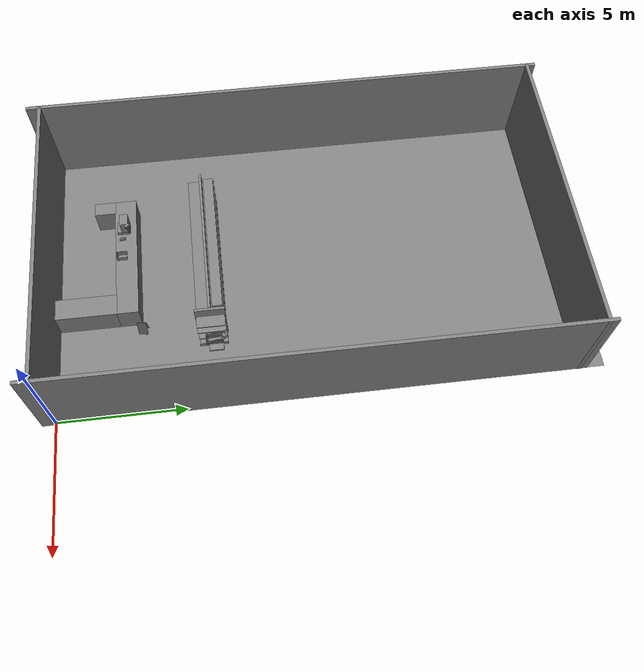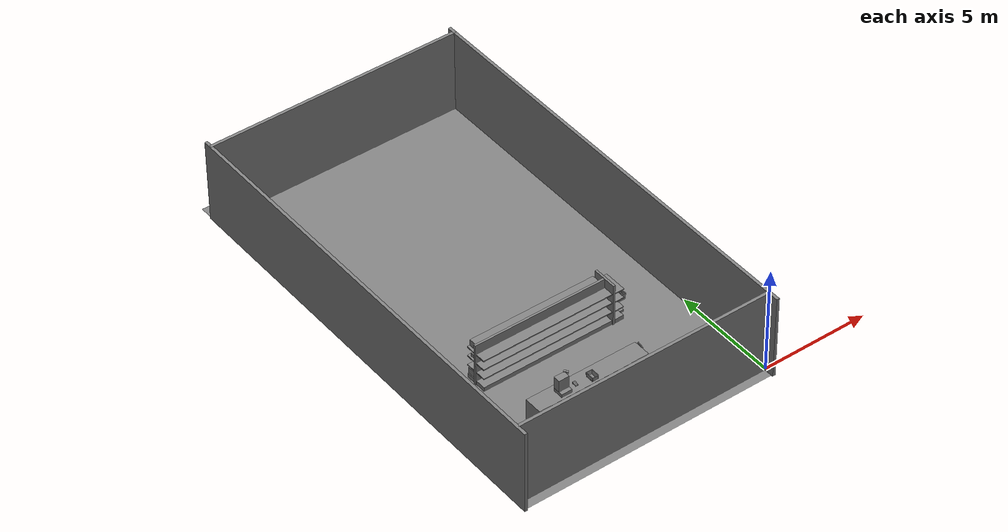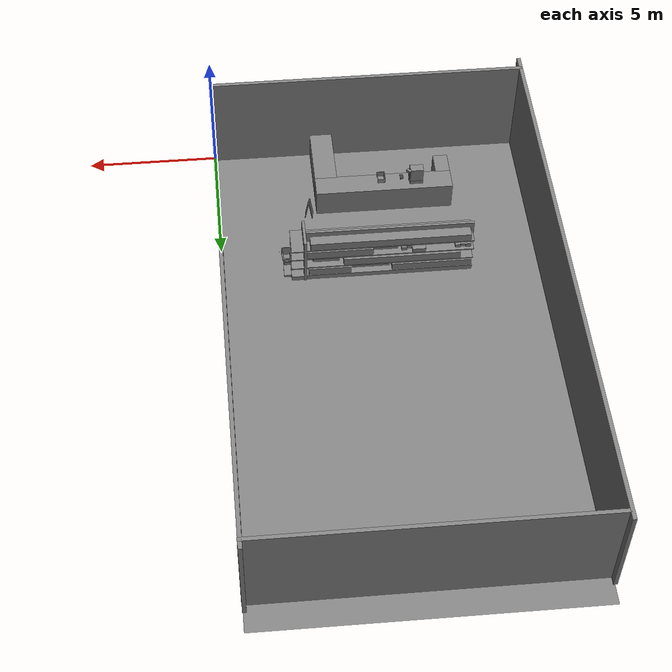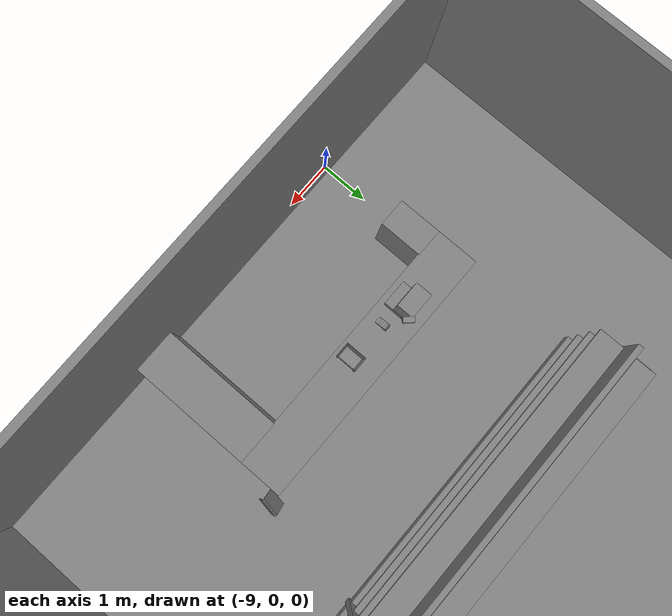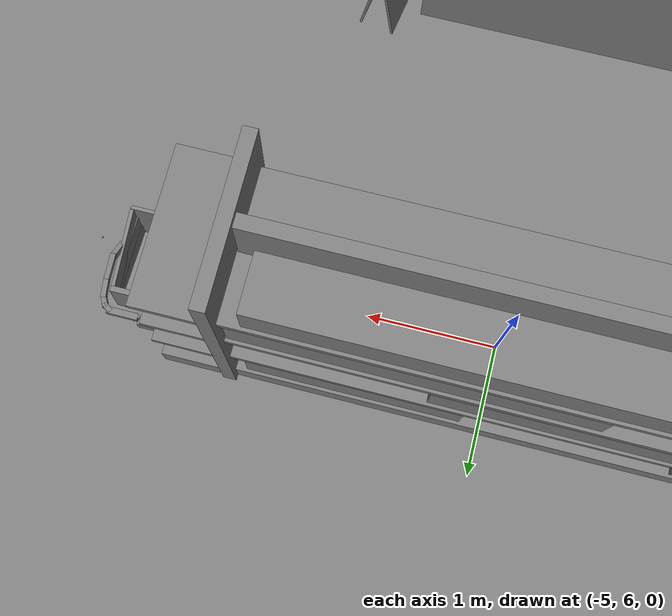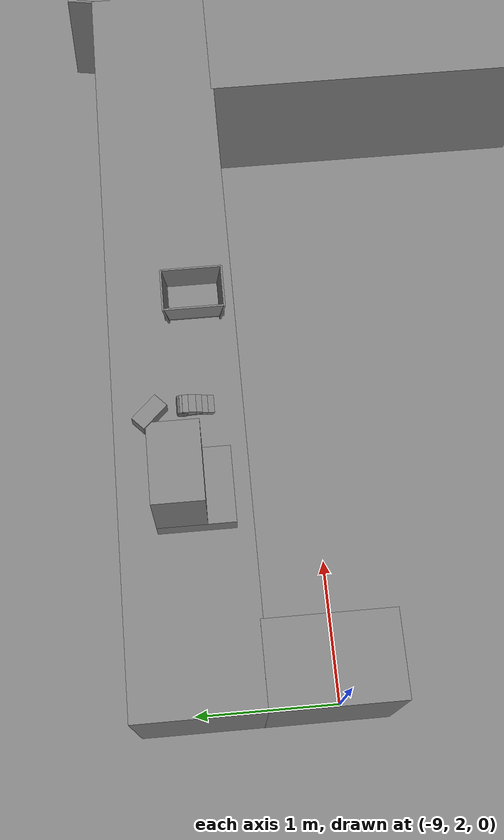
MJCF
<mujoco>
    <option gravity="0.000000000 0.000000000 -9.810000420" timestep="0.0166666" integrator="implicitfast" density="1.225" viscosity="1.8000001e-05" noslip_iterations="10" iterations="100" sdf_iterations="50">
        <flag multiccd="disable"/>
    </option>
    <size memory="1000M"/>
    <compiler coordinate="local"/>
    <worldbody>
        <light cutoff="30" pos="0 1 1" dir="0 -1 -2"/>
        <light cutoff="30" pos="0 -1 1" dir="0 1 -2"/>
        <body pos="-7.168000221 2.823999882 1.227496982" euler="-0.283413887 0.056829713 -0.133293241" name="openloong_gripper_2f85_fix_base_usda_Pos">
            <geom contype="1" conaffinity="1" density="1000" type="box" material="" rgba="0.500000000 0.500000000 0.500000000 1.000000000" solimp="0.899999976 0.949999988 0.001000000" friction="1.000000000 0.005000000 0.000100000" solref="0.020000000 1.000000000" margin="0" condim="3" group="0" pos="-0.002278805 0.074524641 -0.004134178" quat="0.315989256 0.948762834 0.000000000 0.000000000" size="0.059999999 0.013000000 0.035000000" name="openloong_gripper_2f85_fix_base_usda_geom_648E383E_C8C3_4F26_9ACF_C6F5A9B6E276"/>
            <geom contype="1" conaffinity="1" density="1000" type="box" material="" rgba="0.500000000 0.500000000 0.500000000 1.000000000" solimp="0.899999976 0.949999988 0.001000000" friction="1.000000000 0.005000000 0.000100000" solref="0.020000000 1.000000000" margin="0" condim="3" group="0" pos="-0.002278805 0.078031301 0.008128285" quat="0.990447283 -0.137893349 -0.000000000 0.000000000" size="0.059999999 0.010000000 0.035000000" name="openloong_gripper_2f85_fix_base_usda_geom_3EDA985E_E10C_42FF_8FB4_F4091C1746E7"/>
            <geom contype="1" conaffinity="1" density="1000" type="box" material="" rgba="0.500000000 0.500000000 0.500000000 1.000000000" solimp="0.899999976 0.949999988 0.001000000" friction="1.000000000 0.005000000 0.000100000" solref="0.020000000 1.000000000" margin="0" condim="3" group="0" pos="-0.002278805 0.080785275 -0.002596974" quat="0.287325412 -0.957833171 0.000000000 -0.000000000" size="0.059999999 0.013000000 0.035000000" name="openloong_gripper_2f85_fix_base_usda_geom_BD64C44E_FFFE_4EEB_AE6A_66233DAFA8FD"/>
            <geom contype="1" conaffinity="1" density="1000" type="box" material="" rgba="0.500000000 0.500000000 0.500000000 1.000000000" solimp="0.899999976 0.949999988 0.001000000" friction="1.000000000 0.005000000 0.000100000" solref="0.020000000 1.000000000" margin="0" condim="3" group="0" pos="-0.002278805 -0.098804474 -0.020147085" quat="0.988851428 0.148906425 0.000000000 -0.000000000" size="0.059999999 0.022000000 0.020000000" name="openloong_gripper_2f85_fix_base_usda_geom_579BE722_025F_4C5F_A061_9C5716A925A7"/>
            <geom contype="1" conaffinity="1" density="1000" type="box" material="" rgba="0.500000000 0.500000000 0.500000000 1.000000000" solimp="0.899999976 0.949999988 0.001000000" friction="1.000000000 0.005000000 0.000100000" solref="0.020000000 1.000000000" margin="0" condim="3" group="0" pos="-0.002279282 0.019920349 0.012102842" quat="0.995421529 0.095583312 -0.000000000 0.000000000" size="0.059999999 0.025000000 0.026000001" name="openloong_gripper_2f85_fix_base_usda_geom_5F298953_8BA9_4FA5_B587_A1BB6445B4BB"/>
            <geom contype="1" conaffinity="1" density="1000" type="box" material="" rgba="0.500000000 0.500000000 0.500000000 1.000000000" solimp="0.899999976 0.949999988 0.001000000" friction="1.000000000 0.005000000 0.000100000" solref="0.020000000 1.000000000" margin="0" condim="3" group="0" pos="-0.002279282 0.005734444 -0.014276981" quat="0.999571502 -0.029275293 -0.000000000 0.000000000" size="0.059999999 0.050000001 0.010000000" name="openloong_gripper_2f85_fix_base_usda_geom_D6E80ABA_4FAB_43BD_A1EF_4374BC048ED8"/>
            <geom contype="1" conaffinity="1" density="1000" type="box" material="" rgba="0.500000000 0.500000000 0.500000000 1.000000000" solimp="0.899999976 0.949999988 0.001000000" friction="1.000000000 0.005000000 0.000100000" solref="0.020000000 1.000000000" margin="0" condim="3" group="0" pos="-0.002278805 0.079460382 0.007771969" quat="0.922590315 -0.385781497 -0.000000000 0.000000000" size="0.059999999 0.010000000 0.035000000" name="openloong_gripper_2f85_fix_base_usda_geom_01683B35_FDF3_4F44_B515_5214565807AA"/>
            <geom contype="1" conaffinity="1" density="1000" type="box" material="" rgba="0.500000000 0.500000000 0.500000000 1.000000000" solimp="0.899999976 0.949999988 0.001000000" friction="1.000000000 0.005000000 0.000100000" solref="0.020000000 1.000000000" margin="0" condim="3" group="0" pos="-0.002279282 0.081384182 -0.001320124" quat="0.590483606 -0.807049692 0.000000000 0.000000000" size="0.059999999 0.013000000 0.035000000" name="openloong_gripper_2f85_fix_base_usda_geom_71AD3FF4_A1DA_4544_9AF6_32C2E390CE91"/>
            <geom contype="1" conaffinity="1" density="1000" type="box" material="" rgba="0.500000000 0.500000000 0.500000000 1.000000000" solimp="0.899999976 0.949999988 0.001000000" friction="1.000000000 0.005000000 0.000100000" solref="0.020000000 1.000000000" margin="0" condim="3" group="0" pos="-0.002278805 -0.059297562 -0.007972836" quat="0.988851428 0.148906425 0.000000000 -0.000000000" size="0.059999999 0.020000000 0.022000000" name="openloong_gripper_2f85_fix_base_usda_geom_E119A802_5648_4153_8C5F_B502F3914712"/>
            <geom contype="1" conaffinity="1" density="1000" type="box" material="" rgba="0.500000000 0.500000000 0.500000000 1.000000000" solimp="0.899999976 0.949999988 0.001000000" friction="1.000000000 0.005000000 0.000100000" solref="0.020000000 1.000000000" margin="0" condim="3" group="0" pos="-0.002278805 0.076618671 -0.004656911" quat="0.004634960 0.999989390 -0.000000000 0.000000000" size="0.059999999 0.013000000 0.035000000" name="openloong_gripper_2f85_fix_base_usda_geom_EBD69919_CF65_45FF_AAF5_734A044F1605"/>
            <geom contype="1" conaffinity="1" density="1000" type="box" material="" rgba="0.500000000 0.500000000 0.500000000 1.000000000" solimp="0.899999976 0.949999988 0.001000000" friction="1.000000000 0.005000000 0.000100000" solref="0.020000000 1.000000000" margin="0" condim="3" group="0" pos="-0.002279282 -0.021952629 0.002959967" quat="0.991270185 0.131847635 0.000000000 -0.000000000" size="0.059999999 0.020000000 0.024000000" name="openloong_gripper_2f85_fix_base_usda_geom_0DFA5F68_C9A0_4542_A955_F3620D6083C6"/>
            <geom contype="1" conaffinity="1" density="1000" type="box" material="" rgba="0.500000000 0.500000000 0.500000000 1.000000000" solimp="0.899999976 0.949999988 0.001000000" friction="1.000000000 0.005000000 0.000100000" solref="0.020000000 1.000000000" margin="0" condim="3" group="0" pos="-0.002278805 0.081418991 0.002587795" quat="0.803492188 -0.595315576 0.000000000 0.000000000" size="0.059999999 0.013000000 0.035000000" name="openloong_gripper_2f85_fix_base_usda_geom_D16E39D2_DC23_4F89_879C_7FD8C91355D9"/>
            <geom contype="1" conaffinity="1" density="1000" type="box" material="" rgba="0.500000000 0.500000000 0.500000000 1.000000000" solimp="0.899999976 0.949999988 0.001000000" friction="1.000000000 0.005000000 0.000100000" solref="0.020000000 1.000000000" margin="0" condim="3" group="0" pos="-0.002278805 0.061115503 0.008545756" quat="0.999325931 0.036714435 -0.000000000 -0.000000000" size="0.059999999 0.020000000 0.035000000" name="openloong_gripper_2f85_fix_base_usda_geom_7A75BB83_B5B0_4A64_8E55_1B33A96F6AE0"/>
            <freejoint name="openloong_gripper_2f85_fix_base_usda_pos_scan"/>
        </body>
        <body pos="-2.436573029 6.404376507 0.137849092" euler="0.000000000 0.000000000 0.000000000" name="openloong_gripper_2f85_fix_base_usda_shoppingtrolley_01">
            <geom contype="1" conaffinity="1" density="1000" type="box" material="" rgba="0.500000000 0.500000000 0.500000000 1.000000000" solimp="0.899999976 0.949999988 0.001000000" friction="1.000000000 0.005000000 0.000100000" solref="0.020000000 1.000000000" margin="0" condim="3" group="0" pos="-0.169898406 -0.178061336 0.864131629" quat="0.916343808 -0.400392294 -0.000000045 0.000000030" size="0.017999999 0.022499999 0.089999996" name="openloong_gripper_2f85_fix_base_usda_geom_AD5A1D27_92B7_43B0_9E42_815178E20C52"/>
            <geom contype="1" conaffinity="1" density="1000" type="box" material="" rgba="0.500000000 0.500000000 0.500000000 1.000000000" solimp="0.899999976 0.949999988 0.001000000" friction="1.000000000 0.005000000 0.000100000" solref="0.020000000 1.000000000" margin="0" condim="3" group="0" pos="-0.107458733 0.238907143 0.911498845" quat="0.634576976 0.622505128 -0.330067992 -0.317575932" size="0.017999999 0.022499999 0.035999998" name="openloong_gripper_2f85_fix_base_usda_geom_8CBE98B0_B595_4EC3_A922_55E408AF7ED7"/>
            <geom contype="1" conaffinity="1" density="1000" type="box" material="" rgba="0.500000000 0.500000000 0.500000000 1.000000000" solimp="0.899999976 0.949999988 0.001000000" friction="1.000000000 0.005000000 0.000100000" solref="0.020000000 1.000000000" margin="0" condim="3" group="0" pos="-0.005004787 0.248085022 0.912686050" quat="1.000000000 0.000000000 0.000000000 0.000000000" size="0.107999995 0.022499999 0.022499999" name="openloong_gripper_2f85_fix_base_usda_geom_98611E7E_5311_463A_BCD8_94C9DD01192A"/>
            <geom contype="1" conaffinity="1" density="1000" type="box" material="" rgba="0.500000000 0.500000000 0.500000000 1.000000000" solimp="0.899999976 0.949999988 0.001000000" friction="1.000000000 0.005000000 0.000100000" solref="0.020000000 1.000000000" margin="0" condim="3" group="0" pos="0.131482959 -0.182533979 0.598989725" quat="0.996607125 0.055331629 0.059003670 0.015205893" size="0.013499999 0.287999988 0.053999998" name="openloong_gripper_2f85_fix_base_usda_geom_2D3F78EF_33FC_487C_9BFB_E5B31FAE8F2F"/>
            <geom contype="1" conaffinity="1" density="1000" type="box" material="" rgba="0.500000000 0.500000000 0.500000000 1.000000000" solimp="0.899999976 0.949999988 0.001000000" friction="1.000000000 0.005000000 0.000100000" solref="0.020000000 1.000000000" margin="0" condim="3" group="0" pos="-0.000005364 0.100332208 0.734785020" quat="0.999668717 0.025737956 -0.000000010 0.000000000" size="0.135000005 0.019800000 0.152999997" name="openloong_gripper_2f85_fix_base_usda_geom_D1C1486B_200C_4DC1_86DA_4452B92E2A91"/>
            <geom contype="1" conaffinity="1" density="1000" type="box" material="" rgba="0.500000000 0.500000000 0.500000000 1.000000000" solimp="0.899999976 0.949999988 0.001000000" friction="1.000000000 0.005000000 0.000100000" solref="0.020000000 1.000000000" margin="0" condim="3" group="0" pos="-0.126757339 -0.182533979 0.598989725" quat="0.996607184 0.055331606 -0.059003651 -0.015205891" size="0.013499999 0.287999988 0.053999998" name="openloong_gripper_2f85_fix_base_usda_geom_A44767BC_5F92_492A_BCF2_FCB61FE2F8F6"/>
            <geom contype="1" conaffinity="1" density="1000" type="box" material="" rgba="0.500000000 0.500000000 0.500000000 1.000000000" solimp="0.899999976 0.949999988 0.001000000" friction="1.000000000 0.005000000 0.000100000" solref="0.020000000 1.000000000" margin="0" condim="3" group="0" pos="-0.134013891 0.200098798 0.912192523" quat="0.694057047 0.679413557 -0.172947660 -0.163618833" size="0.017999999 0.022499999 0.035999998" name="openloong_gripper_2f85_fix_base_usda_geom_F126EF21_16D6_42B7_8100_E4A1234434B5"/>
            <geom contype="1" conaffinity="1" density="1000" type="box" material="" rgba="0.500000000 0.500000000 0.500000000 1.000000000" solimp="0.899999976 0.949999988 0.001000000" friction="1.000000000 0.005000000 0.000100000" solref="0.020000000 1.000000000" margin="0" condim="3" group="0" pos="0.141839072 -0.191051379 0.702451229" quat="0.997147262 0.056065105 0.045779929 0.021407485" size="0.013499999 0.287999988 0.053999998" name="openloong_gripper_2f85_fix_base_usda_geom_78F450A2_5FCC_45BE_9F0D_5628E0528538"/>
            <geom contype="1" conaffinity="1" density="1000" type="box" material="" rgba="0.500000000 0.500000000 0.500000000 1.000000000" solimp="0.899999976 0.949999988 0.001000000" friction="1.000000000 0.005000000 0.000100000" solref="0.020000000 1.000000000" margin="0" condim="3" group="0" pos="-0.135714188 -0.191051379 0.694841146" quat="0.997147322 0.056064609 -0.045779683 -0.021407485" size="0.013499999 0.287999988 0.053999998" name="openloong_gripper_2f85_fix_base_usda_geom_DD369F85_315A_4B76_970D_A3FF28249D4D"/>
            <geom contype="1" conaffinity="1" density="1000" type="box" material="" rgba="0.500000000 0.500000000 0.500000000 1.000000000" solimp="0.899999976 0.949999988 0.001000000" friction="1.000000000 0.005000000 0.000100000" solref="0.020000000 1.000000000" margin="0" condim="3" group="0" pos="-0.000004721 -0.174527690 0.560063601" quat="0.996704638 0.081116498 -0.000000004 0.000000000" size="0.126000002 0.287999988 0.009000000" name="openloong_gripper_2f85_fix_base_usda_geom_9C9631B4_D3D6_48B0_99E4_9D6F77AA5B5B"/>
            <geom contype="1" conaffinity="1" density="1000" type="box" material="" rgba="0.500000000 0.500000000 0.500000000 1.000000000" solimp="0.899999976 0.949999988 0.001000000" friction="1.000000000 0.005000000 0.000100000" solref="0.020000000 1.000000000" margin="0" condim="3" group="0" pos="0.134013891 0.200098798 0.912192523" quat="0.692574680 -0.680924535 -0.166899428 0.169783980" size="0.017999999 0.022499999 0.035999998" name="openloong_gripper_2f85_fix_base_usda_geom_22779747_EB0D_4314_AE34_D63040DA8DD2"/>
            <geom contype="1" conaffinity="1" density="1000" type="box" material="" rgba="0.500000000 0.500000000 0.500000000 1.000000000" solimp="0.899999976 0.949999988 0.001000000" friction="1.000000000 0.005000000 0.000100000" solref="0.020000000 1.000000000" margin="0" condim="3" group="0" pos="-0.012634277 -0.174527690 -0.088243507" quat="1.000000000 0.000000000 -0.000000004 0.000000000" size="0.135000005 0.287999988 0.044999998" name="openloong_gripper_2f85_fix_base_usda_geom_B84DB671_BDDB_4483_9057_094B989DB2D6"/>
            <geom contype="1" conaffinity="1" density="1000" type="box" material="" rgba="0.500000000 0.500000000 0.500000000 1.000000000" solimp="0.899999976 0.949999988 0.001000000" friction="1.000000000 0.005000000 0.000100000" solref="0.020000000 1.000000000" margin="0" condim="3" group="0" pos="-0.142927840 -0.199506134 0.784674108" quat="0.998421252 0.016904408 -0.027109101 -0.046199299" size="0.013499999 0.305999994 0.063000001" name="openloong_gripper_2f85_fix_base_usda_geom_E5B1E442_5F03_4EAA_9F55_A79750BFF9E2"/>
            <geom contype="1" conaffinity="1" density="1000" type="box" material="" rgba="0.500000000 0.500000000 0.500000000 1.000000000" solimp="0.899999976 0.949999988 0.001000000" friction="1.000000000 0.005000000 0.000100000" solref="0.020000000 1.000000000" margin="0" condim="3" group="0" pos="-0.169898406 -0.043119621 0.915120542" quat="0.687021017 0.726584017 -0.005590606 -0.006832919" size="0.017999999 0.022499999 0.089999996" name="openloong_gripper_2f85_fix_base_usda_geom_CF5ABEEC_4A7A_47B3_983B_E8E7926DD377"/>
            <geom contype="1" conaffinity="1" density="1000" type="box" material="" rgba="0.500000000 0.500000000 0.500000000 1.000000000" solimp="0.899999976 0.949999988 0.001000000" friction="1.000000000 0.005000000 0.000100000" solref="0.020000000 1.000000000" margin="0" condim="3" group="0" pos="-0.000006008 -0.484932661 0.670727849" quat="0.997585475 0.069449045 -0.000000004 -0.000000089" size="0.179999992 0.013499999 0.170999989" name="openloong_gripper_2f85_fix_base_usda_geom_FB1A5EA6_BF74_4F6A_A44B_CA5A1700960B"/>
            <geom contype="1" conaffinity="1" density="1000" type="box" material="" rgba="0.500000000 0.500000000 0.500000000 1.000000000" solimp="0.899999976 0.949999988 0.001000000" friction="1.000000000 0.005000000 0.000100000" solref="0.020000000 1.000000000" margin="0" condim="3" group="0" pos="0.160832971 0.103427693 0.910528183" quat="0.711112797 -0.700149298 -0.042821646 0.047705106" size="0.017999999 0.022499999 0.071999997" name="openloong_gripper_2f85_fix_base_usda_geom_7870E943_B0F5_4240_83CD_CF7B4A87C272"/>
            <geom contype="1" conaffinity="1" density="1000" type="box" material="" rgba="0.500000000 0.500000000 0.500000000 1.000000000" solimp="0.899999976 0.949999988 0.001000000" friction="1.000000000 0.005000000 0.000100000" solref="0.020000000 1.000000000" margin="0" condim="3" group="0" pos="-0.160832763 0.103427693 0.910528183" quat="0.711469591 0.699786782 -0.048386075 -0.042050660" size="0.017999999 0.022499999 0.071999997" name="openloong_gripper_2f85_fix_base_usda_geom_F5057F4D_76E1_451F_A2D9_9DD2F58BCC88"/>
            <geom contype="1" conaffinity="1" density="1000" type="box" material="" rgba="0.500000000 0.500000000 0.500000000 1.000000000" solimp="0.899999976 0.949999988 0.001000000" friction="1.000000000 0.005000000 0.000100000" solref="0.020000000 1.000000000" margin="0" condim="3" group="0" pos="0.169898629 -0.178061336 0.864131629" quat="0.916343808 -0.400392294 -0.000000045 0.000000030" size="0.017999999 0.022499999 0.089999996" name="openloong_gripper_2f85_fix_base_usda_geom_2E53EFF8_C564_4B9F_974D_760C02AF1C37"/>
            <geom contype="1" conaffinity="1" density="1000" type="box" material="" rgba="0.500000000 0.500000000 0.500000000 1.000000000" solimp="0.899999976 0.949999988 0.001000000" friction="1.000000000 0.005000000 0.000100000" solref="0.020000000 1.000000000" margin="0" condim="3" group="0" pos="0.103667587 0.233050480 0.912927270" quat="0.634205043 -0.622199059 -0.324503720 0.324576139" size="0.017999999 0.022499999 0.035999998" name="openloong_gripper_2f85_fix_base_usda_geom_B3FFF8CE_9E47_4220_BA83_F9F3724E7B09"/>
            <geom contype="1" conaffinity="1" density="1000" type="box" material="" rgba="0.500000000 0.500000000 0.500000000 1.000000000" solimp="0.899999976 0.949999988 0.001000000" friction="1.000000000 0.005000000 0.000100000" solref="0.020000000 1.000000000" margin="0" condim="3" group="0" pos="0.169898629 -0.043119621 0.915120542" quat="0.687029123 -0.726576388 -0.006509603 0.005963952" size="0.017999999 0.022499999 0.089999996" name="openloong_gripper_2f85_fix_base_usda_geom_B2AC0ED3_C3B5_4726_9866_60F025D344BC"/>
            <geom contype="1" conaffinity="1" density="1000" type="box" material="" rgba="0.500000000 0.500000000 0.500000000 1.000000000" solimp="0.899999976 0.949999988 0.001000000" friction="1.000000000 0.005000000 0.000100000" solref="0.020000000 1.000000000" margin="0" condim="3" group="0" pos="0.148195267 -0.199506566 0.782808602" quat="0.998808920 0.017156634 0.026950166 0.036880098" size="0.013499999 0.305999994 0.063000001" name="openloong_gripper_2f85_fix_base_usda_geom_D38EC70E_7B8F_482A_91C8_BC41A93AD81D"/>
            <freejoint name="openloong_gripper_2f85_fix_base_usda_shoppingtrolley_01_joint"/>
            <site size="0.005000000 0.005000000 0.005000000" rgba="0.500000000 0.500000000 0.500000000 1.000000000" pos="0.000000000 0.000000000 0.000000000" quat="1.000000000 0.000000000 0.000000000 0.000000000" group="0" type="sphere" name="openloong_gripper_2f85_fix_base_usda_shoppingtrolley_01"/>
        </body>
        <body pos="-6.332345009 2.779978037 1.034067392" euler="0.000000000 0.000000000 0.000000000" name="openloong_gripper_2f85_fix_base_usda_basket">
            <geom contype="1" conaffinity="1" density="100000" type="box" material="" rgba="0.500000000 0.500000000 0.500000000 1.000000000" solimp="0.899999976 0.949999988 0.001000000" friction="1.000000000 0.899999976 0.000100000" solref="0.020000000 1.000000000" margin="0" condim="3" group="0" pos="-0.172339439 0.000000000 0.168361664" quat="0.706172407 -0.036353018 -0.036353093 0.706170976" size="0.200000003 0.006000000 0.108000003" name="openloong_gripper_2f85_fix_base_usda_geom_358E6BC4_E4DF_48EB_B701_59D0FF7318BB"/>
            <geom contype="1" conaffinity="1" density="100000" type="box" material="" rgba="0.500000000 0.500000000 0.500000000 1.000000000" solimp="0.899999976 0.949999988 0.001000000" friction="1.000000000 0.899999976 0.000100000" solref="0.020000000 1.000000000" margin="0" condim="3" group="0" pos="-0.039724827 -0.188568115 0.167089701" quat="0.997537494 0.070135131 0.000000000 0.000000000" size="0.150000006 0.006000000 0.108000003" name="openloong_gripper_2f85_fix_base_usda_geom_114CEE13_4626_411A_8CD4_D2B31C827C56"/>
            <geom contype="1" conaffinity="1" density="100000" type="box" material="" rgba="0.500000000 0.500000000 0.500000000 1.000000000" solimp="0.899999976 0.949999988 0.001000000" friction="1.000000000 0.899999976 0.000100000" solref="0.020000000 1.000000000" margin="0" condim="3" group="0" pos="-0.039724827 0.188377380 0.167089701" quat="0.997489929 -0.070808925 0.000000000 0.000000000" size="0.150000006 0.006000000 0.108000003" name="openloong_gripper_2f85_fix_base_usda_geom_B0513A91_D566_465B_AFAA_FF1D64F21BBF"/>
            <geom contype="1" conaffinity="1" density="100000" type="box" material="" rgba="0.500000000 0.500000000 0.500000000 1.000000000" solimp="0.899999976 0.949999988 0.001000000" friction="1.000000000 0.899999976 0.000100000" solref="0.020000000 1.000000000" margin="0" condim="3" group="0" pos="-0.039724827 0.000000000 0.068126202" quat="1.000000000 0.000000000 0.000000000 0.000000000" size="0.129999995 0.174999997 0.006000000" name="openloong_gripper_2f85_fix_base_usda_geom_9F37DAE2_CA84_44D4_B615_4B426E083DD7"/>
            <geom contype="1" conaffinity="1" density="100000" type="box" material="" rgba="0.500000000 0.500000000 0.500000000 1.000000000" solimp="0.899999976 0.949999988 0.001000000" friction="1.000000000 0.899999976 0.000100000" solref="0.020000000 1.000000000" margin="0" condim="3" group="0" pos="0.094372749 0.000000000 0.168361664" quat="0.706172049 0.036353335 0.036353379 0.706171215" size="0.200000003 0.006000000 0.108000003" name="openloong_gripper_2f85_fix_base_usda_geom_E3843838_0728_44FA_B21F_FD1AB95CB3FE"/>
            <freejoint name="openloong_gripper_2f85_fix_base_usda_basket_joint"/>
            <site size="0.005000000 0.005000000 0.005000000" rgba="0.500000000 0.500000000 0.500000000 1.000000000" pos="0.000000000 0.000000000 0.000000000" quat="1.000000000 0.000000000 0.000000000 0.000000000" group="0" type="sphere" name="openloong_gripper_2f85_fix_base_usda_basketsite"/>
        </body>
        <body pos="-3.510578632 3.403555870 -0.000000100" euler="0.000000000 0.000000000 40.200675964" name="openloong_gripper_2f85_fix_base_usda_PZ">
            <geom contype="1" conaffinity="1" density="1000" type="box" material="" rgba="0.500000000 0.500000000 0.500000000 1.000000000" solimp="0.899999976 0.949999988 0.001000000" friction="1.000000000 0.005000000 0.000100000" solref="0.020000000 1.000000000" margin="0" condim="3" group="0" pos="-0.047453165 0.056484699 0.373715430" quat="0.934750080 0.077914521 0.028795123 0.345459938" size="0.180000007 0.010000000 0.379999995" name="openloong_gripper_2f85_fix_base_usda_geom_78295F14_61CE_4FA6_A600_2DBD1BB8812E"/>
            <geom contype="1" conaffinity="1" density="1000" type="box" material="" rgba="0.500000000 0.500000000 0.500000000 1.000000000" solimp="0.899999976 0.949999988 0.001000000" friction="1.000000000 0.005000000 0.000100000" solref="0.020000000 1.000000000" margin="0" condim="3" group="0" pos="0.047452450 -0.054376602 0.374072611" quat="0.934387863 -0.082143910 -0.030358355 0.345326364" size="0.180000007 0.010000000 0.379999995" name="openloong_gripper_2f85_fix_base_usda_geom_3E88D713_FF98_4DC5_8B4A_CB879FDBF7E8"/>
            <freejoint name="openloong_gripper_2f85_fix_base_usda_PZ"/>
        </body>
        <body pos="0.000000000 0.000000000 0.000000000" euler="0.000000000 0.000000000 0.000000000" name=" Static Objects_ Static Objects">
            <geom contype="1" conaffinity="1" density="1000" type="box" material="" rgba="0.500000000 0.500000000 0.500000000 1.000000000" solimp="0.899999976 0.949999988 0.001000000" friction="1.000000000 0.005000000 0.000100000" solref="0.020000000 1.000000000" margin="0" condim="3" group="0" pos="-3.101639986 6.150595188 1.018643856" quat="1.000000000 0.000000000 0.000000000 0.000000000" size="0.050000001 0.579999983 1.019999981" name=" Static Objects_geom_F728403D_740E_4541_BDF7_3E63CD354174"/>
            <geom contype="1" conaffinity="1" density="1000" type="box" material="" rgba="0.500000000 0.500000000 0.500000000 1.000000000" solimp="0.899999976 0.949999988 0.001000000" friction="1.000000000 0.005000000 0.000100000" solref="0.020000000 1.000000000" margin="0" condim="3" group="0" pos="-2.825197220 6.153595448 1.115278244" quat="0.707107067 0.000000000 0.000000000 0.707106471" size="0.550000012 0.239999995 0.025000000" name=" Static Objects_geom_380D28A3_4896_4394_A727_9023B013C502"/>
            <geom contype="1" conaffinity="1" density="1000" type="box" material="" rgba="0.500000000 0.500000000 0.500000000 1.000000000" solimp="0.899999976 0.949999988 0.001000000" friction="1.000000000 0.005000000 0.000100000" solref="0.020000000 1.000000000" margin="0" condim="3" group="0" pos="-2.825197220 6.153595448 0.097434282" quat="0.707107067 0.000000000 0.000000000 0.707106471" size="0.550000012 0.239999995 0.098999999" name=" Static Objects_geom_4649ED79_C8D8_406A_AB10_7AEF0D3A8891"/>
            <geom contype="1" conaffinity="1" density="1000" type="box" material="" rgba="0.500000000 0.500000000 0.500000000 1.000000000" solimp="0.899999976 0.949999988 0.001000000" friction="1.000000000 0.005000000 0.000100000" solref="0.020000000 1.000000000" margin="0" condim="3" group="0" pos="-6.293097973 6.153595448 1.114443064" quat="0.707107067 0.000000000 0.000000000 0.707106471" size="0.529999971 3.134999990 0.025000000" name=" Static Objects_geom_C1DC21C5_0672_443B_90AB_1646014E966C"/>
            <geom contype="1" conaffinity="1" density="1000" type="box" material="" rgba="0.500000000 0.500000000 0.500000000 1.000000000" solimp="0.899999976 0.949999988 0.001000000" friction="1.000000000 0.005000000 0.000100000" solref="0.020000000 1.000000000" margin="0" condim="3" group="0" pos="-6.286010742 6.153595448 0.096129179" quat="0.707107067 0.000000000 0.000000000 0.707106471" size="0.529999971 3.134999990 0.098999999" name=" Static Objects_geom_BAC7E97A_3F34_4CC8_8D74_BA6B9594D335"/>
            <geom contype="1" conaffinity="1" density="1000" type="box" material="" rgba="0.500000000 0.500000000 0.500000000 1.000000000" solimp="0.899999976 0.949999988 0.001000000" friction="1.000000000 0.005000000 0.000100000" solref="0.020000000 1.000000000" margin="0" condim="3" group="0" pos="-2.825197220 6.153595448 1.563861728" quat="0.707107067 0.000000000 0.000000000 0.707106471" size="0.550000012 0.239999995 0.025000000" name=" Static Objects_geom_BFA14DFF_7018_4B56_90F4_2719D3A7A7E5"/>
            <geom contype="1" conaffinity="1" density="1000" type="box" material="" rgba="0.500000000 0.500000000 0.500000000 1.000000000" solimp="0.899999976 0.949999988 0.001000000" friction="1.000000000 0.005000000 0.000100000" solref="0.020000000 1.000000000" margin="0" condim="3" group="0" pos="-6.311686516 6.153595448 1.018643856" quat="0.707107067 0.000000000 0.000000000 0.707106471" size="0.050000001 3.150000095 1.019999981" name=" Static Objects_geom_59EA98D9_D20E_4260_8A00_575B5AD15BC7"/>
            <geom contype="1" conaffinity="1" density="1000" type="box" material="" rgba="0.500000000 0.500000000 0.500000000 1.000000000" solimp="0.899999976 0.949999988 0.001000000" friction="1.000000000 0.005000000 0.000100000" solref="0.020000000 1.000000000" margin="0" condim="3" group="0" pos="-2.825197220 6.153595448 0.629031777" quat="0.707107067 0.000000000 0.000000000 0.707106471" size="0.550000012 0.239999995 0.025000000" name=" Static Objects_geom_37AE2866_4A78_4BF5_8676_5ACEB8F75060"/>
            <geom contype="1" conaffinity="1" density="1000" type="box" material="" rgba="0.500000000 0.500000000 0.500000000 1.000000000" solimp="0.899999976 0.949999988 0.001000000" friction="1.000000000 0.005000000 0.000100000" solref="0.020000000 1.000000000" margin="0" condim="3" group="0" pos="-6.286010742 6.153595448 1.563861728" quat="0.707107067 0.000000000 0.000000000 0.707106471" size="0.529999971 3.134999990 0.025000000" name=" Static Objects_geom_4B4DCB46_EA33_4266_84B4_33D3AE915D09"/>
            <geom contype="1" conaffinity="1" density="1000" type="box" material="" rgba="0.500000000 0.500000000 0.500000000 1.000000000" solimp="0.899999976 0.949999988 0.001000000" friction="1.000000000 0.005000000 0.000100000" solref="0.020000000 1.000000000" margin="0" condim="3" group="0" pos="-6.286010742 6.153595448 0.629031777" quat="0.707107067 0.000000000 0.000000000 0.707106471" size="0.529999971 3.134999990 0.025000000" name=" Static Objects_geom_49F8D5D1_7319_4B32_8F4D_0298D54A244F"/>
            <geom contype="1" conaffinity="1" density="1000" type="box" material="" rgba="0.500000000 0.500000000 0.500000000 1.000000000" solimp="0.899999976 0.949999988 0.001000000" friction="1.000000000 0.005000000 0.000100000" solref="0.020000000 1.000000000" margin="0" condim="3" group="0" pos="-7.719123363 2.867671013 1.173410416" quat="1.000000000 0.000000000 0.000000000 0.000000000" size="0.250000000 0.250000000 0.079999998" name=" Static Objects_geom_8A312B48_F234_4B0B_A05C_A60011A28D8C"/>
            <geom contype="1" conaffinity="1" density="1000" type="box" material="" rgba="0.500000000 0.500000000 0.500000000 1.000000000" solimp="0.899999976 0.949999988 0.001000000" friction="1.000000000 0.005000000 0.000100000" solref="0.020000000 1.000000000" margin="0" condim="3" group="0" pos="-7.408766270 3.088089943 1.776644945" quat="0.928051054 0.000000000 0.000000000 0.372453064" size="0.050000001 0.100000001 0.050000001" name=" Static Objects_geom_A2E93BE1_372F_4F65_BBF0_E29B2F88725B"/>
            <geom contype="1" conaffinity="1" density="1000" type="box" material="" rgba="0.500000000 0.500000000 0.500000000 1.000000000" solimp="0.899999976 0.949999988 0.001000000" friction="1.000000000 0.005000000 0.000100000" solref="0.020000000 1.000000000" margin="0" condim="3" group="0" pos="-7.719123363 2.958004713 1.530241251" quat="1.000000000 0.000000000 0.000000000 0.000000000" size="0.250000000 0.159999996 0.280000001" name=" Static Objects_geom_B25E7511_9D98_448F_A546_F6F1F86F6027"/>
            <geom contype="1" conaffinity="1" density="1000" type="cylinder" material="" rgba="0.500000000 0.500000000 0.500000000 1.000000000" solimp="0.899999976 0.949999988 0.001000000" friction="1.000000000 0.005000000 0.000100000" solref="0.020000000 1.000000000" margin="0" condim="3" group="0" pos="-7.427312374 3.069516420 1.502544641" quat="0.928051054 0.000000000 0.000000000 0.372453064" size="0.015000000 0.230000004 0.100000001" name=" Static Objects_geom_17B05CAF_9BA4_4205_AFC7_D97C6472737A"/>
            <geom contype="1" conaffinity="1" density="1000" type="box" material="" rgba="0.500000000 0.500000000 0.500000000 1.000000000" solimp="0.899999976 0.949999988 0.001000000" friction="1.000000000 0.005000000 0.000100000" solref="0.020000000 1.000000000" margin="0" condim="3" group="0" pos="-7.437745571 3.067511320 1.289965630" quat="1.000000000 0.000000000 0.000000000 0.000000000" size="0.029999999 0.020000000 0.020000000" name=" Static Objects_geom_9C83C0C7_5B9D_4AD9_B3CF_60CCCDE85F13"/>
            <geom contype="1" conaffinity="1" density="1000" type="box" material="" rgba="0.500000000 0.500000000 0.500000000 1.000000000" solimp="0.899999976 0.949999988 0.001000000" friction="1.000000000 0.005000000 0.000100000" solref="0.020000000 1.000000000" margin="0" condim="3" group="0" pos="-9.058088303 6.434794426 1.209077358" quat="1.000000000 0.000000000 0.000000000 0.000000000" size="0.250000000 0.100000001 0.070000000" name=" Static Objects_geom_125DFC6C_5E17_41C2_9C43_91D5051FC062"/>
            <geom contype="1" conaffinity="1" density="1000" type="box" material="" rgba="0.500000000 0.500000000 0.500000000 1.000000000" solimp="0.899999976 0.949999988 0.001000000" friction="1.000000000 0.005000000 0.000100000" solref="0.020000000 1.000000000" margin="0" condim="3" group="0" pos="-7.886891365 6.459744930 0.352518857" quat="1.000000000 0.000000000 0.000000000 0.000000000" size="1.500000000 0.200000003 0.150000006" name=" Static Objects_geom_6D9BC12C_46A1_49C5_A0EA_6C2978D2E47B"/>
            <geom contype="1" conaffinity="1" density="1000" type="box" material="" rgba="0.500000000 0.500000000 0.500000000 1.000000000" solimp="0.899999976 0.949999988 0.001000000" friction="1.000000000 0.005000000 0.000100000" solref="0.020000000 1.000000000" margin="0" condim="3" group="0" pos="-9.237723351 6.464855671 1.209077358" quat="1.000000000 0.000000000 0.000000000 0.000000000" size="0.100000001 0.100000001 0.070000000" name=" Static Objects_geom_8BCBD50B_0AC4_40E7_AF10_DACD4E055F85"/>
            <geom contype="1" conaffinity="1" density="1000" type="box" material="" rgba="0.500000000 0.500000000 0.500000000 1.000000000" solimp="0.899999976 0.949999988 0.001000000" friction="1.000000000 0.005000000 0.000100000" solref="0.020000000 1.000000000" margin="0" condim="3" group="0" pos="-6.924745083 6.362090111 1.214329123" quat="1.000000000 0.000000000 0.000000000 0.000000000" size="0.200000003 0.100000001 0.075000003" name=" Static Objects_geom_10F49F1E_7C1D_4BFA_8DC8_E52BA5A7185C"/>
            <geom contype="1" conaffinity="1" density="1000" type="box" material="" rgba="0.500000000 0.500000000 0.500000000 1.000000000" solimp="0.899999976 0.949999988 0.001000000" friction="1.000000000 0.005000000 0.000100000" solref="0.020000000 1.000000000" margin="0" condim="3" group="0" pos="-4.407354832 6.459744930 1.292199373" quat="1.000000000 0.000000000 0.000000000 0.000000000" size="1.240000010 0.200000003 0.150000006" name=" Static Objects_geom_08FBA313_7D55_4127_A886_C3F7490AD3CF"/>
            <geom contype="1" conaffinity="1" density="1000" type="box" material="" rgba="0.500000000 0.500000000 0.500000000 1.000000000" solimp="0.899999976 0.949999988 0.001000000" friction="1.000000000 0.005000000 0.000100000" solref="0.020000000 1.000000000" margin="0" condim="3" group="0" pos="-5.611940861 6.318420410 0.350975692" quat="1.000000000 0.000000000 0.000000000 0.000000000" size="0.699999988 0.100000001 0.150000006" name=" Static Objects_geom_655A1163_9A51_4F83_AF65_D234086FE987"/>
            <geom contype="1" conaffinity="1" density="1000" type="box" material="" rgba="0.500000000 0.500000000 0.500000000 1.000000000" solimp="0.899999976 0.949999988 0.001000000" friction="1.000000000 0.005000000 0.000100000" solref="0.020000000 1.000000000" margin="0" condim="3" group="0" pos="-6.300771236 6.459744930 1.744376063" quat="1.000000000 0.000000000 0.000000000 0.000000000" size="3.000000000 0.200000003 0.150000006" name=" Static Objects_geom_7EE03A2C_986A_4593_8DDA_20A2E9ECCF82"/>
            <geom contype="1" conaffinity="1" density="1000" type="box" material="" rgba="0.500000000 0.500000000 0.500000000 1.000000000" solimp="0.899999976 0.949999988 0.001000000" friction="1.000000000 0.005000000 0.000100000" solref="0.020000000 1.000000000" margin="0" condim="3" group="0" pos="-6.751636982 6.459744930 0.800981164" quat="1.000000000 0.000000000 0.000000000 0.000000000" size="2.200000048 0.200000003 0.150000006" name=" Static Objects_geom_5A13DA76_3084_4B56_84D1_1B544F4122F4"/>
            <geom contype="1" conaffinity="1" density="1000" type="box" material="" rgba="0.500000000 0.500000000 0.500000000 1.000000000" solimp="0.899999976 0.949999988 0.001000000" friction="1.000000000 0.005000000 0.000100000" solref="0.020000000 1.000000000" margin="0" condim="3" group="0" pos="-8.844120979 6.464855671 1.209077358" quat="1.000000000 0.000000000 0.000000000 0.000000000" size="0.100000001 0.100000001 0.070000000" name=" Static Objects_geom_C2FC0652_F289_4524_A20F_5D0186E3013D"/>
            <geom contype="1" conaffinity="1" density="1000" type="box" material="" rgba="0.500000000 0.500000000 0.500000000 1.000000000" solimp="0.899999976 0.949999988 0.001000000" friction="1.000000000 0.005000000 0.000100000" solref="0.020000000 1.000000000" margin="0" condim="3" group="0" pos="-6.098561764 6.327973843 1.292199373" quat="1.000000000 0.000000000 0.000000000 0.000000000" size="0.500000000 0.100000001 0.150000006" name=" Static Objects_geom_4450DC85_D57C_4770_974A_59BC4F00D9B9"/>
            <geom contype="1" conaffinity="1" density="1000" type="box" material="" rgba="0.500000000 0.500000000 0.500000000 1.000000000" solimp="0.899999976 0.949999988 0.001000000" friction="1.000000000 0.005000000 0.000100000" solref="0.020000000 1.000000000" margin="0" condim="3" group="0" pos="-6.824534416 6.447464466 1.212718010" quat="1.000000000 0.000000000 0.000000000 0.000000000" size="0.100000001 0.100000001 0.075000003" name=" Static Objects_geom_4B511423_88EF_4AA6_A76F_2184F936C094"/>
            <geom contype="1" conaffinity="1" density="1000" type="box" material="" rgba="0.500000000 0.500000000 0.500000000 1.000000000" solimp="0.899999976 0.949999988 0.001000000" friction="1.000000000 0.005000000 0.000100000" solref="0.020000000 1.000000000" margin="0" condim="3" group="0" pos="-3.907610416 6.318625927 0.800981164" quat="1.000000000 0.000000000 0.000000000 0.000000000" size="0.500000000 0.100000001 0.150000006" name=" Static Objects_geom_20A37875_CF92_4E39_B289_79DEA60D4603"/>
            <geom contype="1" conaffinity="1" density="1000" type="box" material="" rgba="0.500000000 0.500000000 0.500000000 1.000000000" solimp="0.899999976 0.949999988 0.001000000" friction="1.000000000 0.005000000 0.000100000" solref="0.020000000 1.000000000" margin="0" condim="3" group="0" pos="-7.373087406 6.458900928 1.214329123" quat="1.000000000 0.000000000 0.000000000 0.000000000" size="0.250000000 0.200000003 0.075000003" name=" Static Objects_geom_E3729C7D_D042_4B1F_A735_75900EBB414A"/>
            <geom contype="1" conaffinity="1" density="1000" type="box" material="" rgba="0.500000000 0.500000000 0.500000000 1.000000000" solimp="0.899999976 0.949999988 0.001000000" friction="1.000000000 0.005000000 0.000100000" solref="0.020000000 1.000000000" margin="0" condim="3" group="0" pos="-4.035642624 6.459744930 0.352518857" quat="1.000000000 0.000000000 0.000000000 0.000000000" size="0.800000012 0.200000003 0.150000006" name=" Static Objects_geom_2854C7D7_DA31_4A2C_A9AB_8A1B99680420"/>
            <geom contype="1" conaffinity="1" density="1000" type="box" material="" rgba="0.500000000 0.500000000 0.500000000 1.000000000" solimp="0.899999976 0.949999988 0.001000000" friction="1.000000000 0.005000000 0.000100000" solref="0.020000000 1.000000000" margin="0" condim="3" group="0" pos="-6.460197449 2.937205315 0.548931718" quat="1.000000000 0.000000000 0.000000000 0.000000000" size="2.650000095 0.430000007 0.550000012" name=" Static Objects_geom_6F2F7124_3DE1_4086_BC5D_7041013F60E1"/>
            <geom contype="1" conaffinity="1" density="1000" type="box" material="" rgba="0.500000000 0.500000000 0.500000000 1.000000000" solimp="0.899999976 0.949999988 0.001000000" friction="1.000000000 0.005000000 0.000100000" solref="0.020000000 1.000000000" margin="0" condim="3" group="0" pos="-4.240264893 1.327049494 0.549888909" quat="1.000000000 0.000000000 0.000000000 0.000000000" size="0.430000007 1.200000048 0.550000012" name=" Static Objects_geom_2F2214F3_CC80_4EBE_804E_D325C4474803"/>
            <geom contype="1" conaffinity="1" density="1000" type="box" material="" rgba="0.500000000 0.500000000 0.500000000 1.000000000" solimp="0.899999976 0.949999988 0.001000000" friction="1.000000000 0.005000000 0.000100000" solref="0.020000000 1.000000000" margin="0" condim="3" group="0" pos="-8.830721855 2.096410990 0.549305558" quat="1.000000000 0.000000000 0.000000000 0.000000000" size="0.280000001 0.430000007 0.550000012" name=" Static Objects_geom_C3D72474_7487_441A_AFF5_5B7801567CF9"/>
            <geom contype="1" conaffinity="1" density="1000" type="plane" material="" rgba="0.500000000 0.500000000 0.500000000 1.000000000" solimp="0.899999976 0.949999988 0.001000000" friction="1.000000000 0.005000000 0.000100000" solref="0.020000000 1.000000000" margin="0" condim="3" group="0" pos="-6.000000000 10.399999619 0.000000000" quat="1.000000000 0.000000000 0.000000000 0.000000000" size="6.050000191 10.800000191 0.010000000" name=" Static Objects_geom_4AD8178B_58A4_48DC_BB4F_3EAD861BE39C"/>
            <geom contype="1" conaffinity="1" density="1000" type="box" material="" rgba="0.500000000 0.500000000 0.500000000 1.000000000" solimp="0.899999976 0.949999988 0.001000000" friction="1.000000000 0.005000000 0.000100000" solref="0.020000000 1.000000000" margin="0" condim="3" group="0" pos="-6.000000000 0.035000000 2.000000000" quat="1.000000000 0.000000000 0.000000000 0.000000000" size="6.079999924 0.070000000 2.000000000" name=" Static Objects_geom_7B0A8A72_EB05_45DA_851C_875449A9B700"/>
            <geom contype="1" conaffinity="1" density="1000" type="box" material="" rgba="0.500000000 0.500000000 0.500000000 1.000000000" solimp="0.899999976 0.949999988 0.001000000" friction="1.000000000 0.005000000 0.000100000" solref="0.020000000 1.000000000" margin="0" condim="3" group="0" pos="-6.000000000 20.159999847 2.000000000" quat="1.000000000 0.000000000 0.000000000 0.000000000" size="6.079999924 0.070000000 2.000000000" name=" Static Objects_geom_5FB7B7F1_891C_4FEE_A0C3_6B0B9DDE95B1"/>
            <geom contype="1" conaffinity="1" density="1000" type="box" material="" rgba="0.500000000 0.500000000 0.500000000 1.000000000" solimp="0.899999976 0.949999988 0.001000000" friction="1.000000000 0.005000000 0.000100000" solref="0.020000000 1.000000000" margin="0" condim="3" group="0" pos="0.000000000 10.000000000 2.000000000" quat="1.000000000 0.000000000 0.000000000 0.000000000" size="0.070000000 10.500000000 2.000000000" name=" Static Objects_geom_5541ED24_5850_4529_BD95_36791A315495"/>
            <geom contype="1" conaffinity="1" density="1000" type="box" material="" rgba="0.500000000 0.500000000 0.500000000 1.000000000" solimp="0.899999976 0.949999988 0.001000000" friction="1.000000000 0.005000000 0.000100000" solref="0.020000000 1.000000000" margin="0" condim="3" group="0" pos="-12.050000191 10.000000000 2.000000000" quat="1.000000000 0.000000000 0.000000000 0.000000000" size="0.070000000 10.500000000 2.000000000" name=" Static Objects_geom_9E32D3F9_1695_4E98_9DB2_DC13B363222D"/>
        </body>
        <body pos="0.000000000 0.000000000 0.000000000" euler="0.000000000 0.000000000 0.000000000" name="Interactive Objects_Interactive Objects"/>
        <body pos="-2.162787437 6.180304527 -0.123990886" euler="0.000000000 0.000000000 180.000000000" mocap="true" name="openloong_gripper_2f85_fix_base_usda_leftHandMocap"/>
        <body pos="-2.162787437 6.180304527 -0.123990886" euler="0.000000000 0.000000000 180.000000000" mocap="true" name="openloong_gripper_2f85_fix_base_usda_rightHandMocap"/>
        <body pos="-2.162787437 6.180304527 1.076009154" euler="0.000000000 0.000000000 180.000000000" name="openloong_gripper_2f85_fix_base_usda_base_link">
            <geom contype="1" conaffinity="1" density="1000" type="mesh" material="" rgba="0.783999979 0.783999979 0.783999979 1.000000000" solimp="0.899999976 0.949999988 0.001000000" friction="1.000000000 0.005000000 0.000100000" solref="0.020000000 1.000000000" margin="0" condim="3" group="3" mesh="base_link" pos="0.000000000 0.000000000 0.000000000" quat="1.000000000 0.000000000 0.000000000 0.000000000" size="1.000000000 1.000000000 1.000000000" name="openloong_gripper_2f85_fix_base_usda__geom_7_F4A18868_8C48_48AC_99A6_957347EF538C"/>
            <site size="0.005000000 0.005000000 0.005000000" rgba="0.500000000 0.500000000 0.500000000 1.000000000" pos="0.000000000 0.000000000 0.000000000" quat="1.000000000 0.000000000 0.000000000 0.000000000" group="0" type="sphere" name="openloong_gripper_2f85_fix_base_usda_imu"/>
            <inertial mass="22.447001" pos="-0.005664100 -0.001336700 0.238289997" diaginertia="0.374352545 0.277180195 0.220617250" quat="0.999247074 0.035235517 -0.015086859 0.006023135"/>
            <body pos="0.000000000 0.000000000 0.300000072" euler="0.000000000 0.000000000 0.000000000" name="openloong_gripper_2f85_fix_base_usda_dummy_body">
                <geom contype="1" conaffinity="1" density="1000" type="sphere" material="" rgba="0.783999979 0.783999979 0.783999979 1.000000000" solimp="0.899999976 0.949999988 0.001000000" friction="1.000000000 0.005000000 0.000100000" solref="0.020000000 1.000000000" margin="0" condim="3" group="3" pos="0.000000000 0.000000000 0.000000000" quat="1.000000000 0.000000000 0.000000000 0.000000000" size="0.010000000 0.000000000 0.000000000" name="openloong_gripper_2f85_fix_base_usda__geom_8_B49D0C51_C16A_4FE4_A05F_FFC9BA72F24D"/>
                <joint armature="0.0099999998" stiffness="0" damping="0.1" axis="0.000000 0.000000 1.000000" type="hinge" name="openloong_gripper_2f85_fix_base_usda_dummy_joint"/>
                <site size="0.010000000 0.005000000 0.005000000" rgba="0.500000000 0.500000000 0.500000000 1.000000000" pos="0.000000000 0.000000000 0.000000000" quat="1.000000000 0.000000000 0.000000000 0.000000000" group="3" type="sphere" name="openloong_gripper_2f85_fix_base_usda_dummy_site"/>
            </body>
            <body pos="0.009000063 0.000000000 0.406399965" euler="0.000000000 0.000000000 0.000000000" name="openloong_gripper_2f85_fix_base_usda_Link_head_yaw">
                <geom contype="1" conaffinity="1" density="1000" type="mesh" material="" rgba="0.783999979 0.783999979 0.783999979 1.000000000" solimp="0.899999976 0.949999988 0.001000000" friction="1.000000000 0.005000000 0.000100000" solref="0.020000000 1.000000000" margin="0" condim="3" group="3" mesh="Link_head_yaw" pos="0.000000000 0.000000000 0.000000000" quat="1.000000000 0.000000000 0.000000000 0.000000000" size="1.000000000 1.000000000 1.000000000" name="openloong_gripper_2f85_fix_base_usda__geom_10_07025B93_50CD_4983_A4E8_89BD3A0EA074"/>
                <inertial mass="0.84249002" pos="0.000000000 -0.002081400 0.044801001" diaginertia="0.000700588 0.000629000 0.000553812" quat="0.706933022 -0.015675601 0.015677100 0.706933022"/>
                <body pos="0.000000000 -0.034599781 0.048499942" euler="0.000000000 0.000000000 0.000000000" name="openloong_gripper_2f85_fix_base_usda_Link_head_pitch">
                    <geom contype="1" conaffinity="1" density="1000" type="mesh" material="" rgba="0.783999979 0.783999979 0.783999979 1.000000000" solimp="0.899999976 0.949999988 0.001000000" friction="1.000000000 0.005000000 0.000100000" solref="0.020000000 1.000000000" margin="0" condim="3" group="3" mesh="Link_head_pitch" pos="0.000000000 0.000000000 0.000000000" quat="1.000000000 0.000000000 0.000000000 0.000000000" size="1.000000000 1.000000000 1.000000000" name="openloong_gripper_2f85_fix_base_usda__geom_12_5F47C97A_D42C_40B8_80A9_FAB9F9DF7EAB"/>
                    <inertial mass="1.3943" pos="0.020569000 0.033004001 0.125000000" diaginertia="0.006381400 0.006289940 0.004481460" quat="0.973390222 0.008406822 0.228157058 0.019624906"/>
                    <body pos="0.000000000 0.030000210 0.000000000" euler="0.000000000 0.000000000 0.000000000" name="openloong_gripper_2f85_fix_base_usda_neck_center_body">
                        <site size="0.010000000 0.005000000 0.005000000" rgba="0.500000000 0.500000000 0.500000000 1.000000000" pos="0.000000000 0.000000000 0.000000000" quat="1.000000000 0.000000000 0.000000000 0.000000000" group="3" type="sphere" name="openloong_gripper_2f85_fix_base_usda_neck_center_site"/>
                        <body pos="0.019999981 0.000000000 0.149999976" euler="-0.000002229 39.998176575 -90.000205994" name="openloong_gripper_2f85_fix_base_usda_camera_head">
                            <site size="0.010000000 0.005000000 0.005000000" rgba="0.500000000 0.500000000 0.500000000 1.000000000" pos="0.000000000 0.000000000 0.000000000" quat="1.000000000 0.000000000 0.000000000 0.000000000" group="3" type="sphere" name="openloong_gripper_2f85_fix_base_usda_camera_head_site"/>
                        </body>
                    </body>
                </body>
            </body>
            <body pos="0.003999949 -0.161600113 0.392199993" euler="0.000000000 0.000000000 0.000000000" name="openloong_gripper_2f85_fix_base_usda_Link_arm_r_01">
                <geom contype="1" conaffinity="1" density="1000" type="mesh" material="" rgba="0.783999979 0.783999979 0.783999979 1.000000000" solimp="0.899999976 0.949999988 0.001000000" friction="1.000000000 0.005000000 0.000100000" solref="0.020000000 1.000000000" margin="0" condim="3" group="3" mesh="Link_arm_r_01" pos="0.000000000 0.000000000 0.000000000" quat="1.000000000 0.000000000 0.000000000 0.000000000" size="1.000000000 1.000000000 1.000000000" name="openloong_gripper_2f85_fix_base_usda__geom_14_A6756777_E3B4_4DB9_BBB4_F342F5EE34CE"/>
                <joint armature="0.0099999998" stiffness="0" damping="1" axis="0.000000 -1.000000 0.000000" limited="true" range="-170.000015259 170.000015259" type="hinge" name="openloong_gripper_2f85_fix_base_usda_J_arm_r_01"/>
                <inertial mass="0.75641" pos="0.004494600 -0.038293999 -0.000001874" diaginertia="0.000842990 0.000803050 0.000587120" quat="-0.000163502 0.707098067 0.000812463 0.707115054"/>
                <body pos="-0.042000055 -0.040999889 0.000000000" euler="0.000000000 0.000000000 0.000000000" name="openloong_gripper_2f85_fix_base_usda_Link_arm_r_02">
                    <geom contype="1" conaffinity="1" density="1000" type="mesh" material="" rgba="0.783999979 0.783999979 0.783999979 1.000000000" solimp="0.899999976 0.949999988 0.001000000" friction="1.000000000 0.005000000 0.000100000" solref="0.020000000 1.000000000" margin="0" condim="3" group="3" mesh="Link_arm_r_02" pos="0.000000000 0.000000000 0.000000000" quat="1.000000000 0.000000000 0.000000000 0.000000000" size="1.000000000 1.000000000 1.000000000" name="openloong_gripper_2f85_fix_base_usda__geom_16_7345AC4D_7CF9_4570_A0A2_F713D66977FF"/>
                    <joint armature="0.0099999998" stiffness="0" damping="1" axis="-1.000000 0.000000 0.000000" limited="true" range="-105.000244141 105.000244141" type="hinge" name="openloong_gripper_2f85_fix_base_usda_J_arm_r_02"/>
                    <inertial mass="0.98500001" pos="0.041999999 -0.067430697 0.000000000" diaginertia="0.002262690 0.001730990 0.001154020" quat="0.500000000 0.500000000 -0.500000000 0.500000000"/>
                    <body pos="0.042000055 -0.122600079 0.000000000" euler="0.000000000 0.000000000 0.000000000" name="openloong_gripper_2f85_fix_base_usda_Link_arm_r_03">
                        <geom contype="1" conaffinity="1" density="1000" type="mesh" material="" rgba="0.783999979 0.783999979 0.783999979 1.000000000" solimp="0.899999976 0.949999988 0.001000000" friction="1.000000000 0.005000000 0.000100000" solref="0.020000000 1.000000000" margin="0" condim="3" group="3" mesh="Link_arm_r_03" pos="0.000000000 0.000000000 0.000000000" quat="1.000000000 0.000000000 0.000000000 0.000000000" size="1.000000000 1.000000000 1.000000000" name="openloong_gripper_2f85_fix_base_usda__geom_18_99AB5D0A_047F_41D5_8016_7B076FD5C46E"/>
                        <joint armature="0.0099999998" stiffness="0" damping="1" axis="0.000000 -1.000000 0.000000" limited="true" range="-170.000015259 170.000015259" type="hinge" name="openloong_gripper_2f85_fix_base_usda_J_arm_r_03"/>
                        <inertial mass="0.95899999" pos="-0.001413580 -0.164663002 0.020757901" diaginertia="0.002101340 0.002064590 0.000754802" quat="0.560480952 0.454391927 -0.443732947 0.531497955"/>
                        <body pos="0.035300016 -0.177400112 0.024000049" euler="0.000000000 0.000000000 0.000000000" name="openloong_gripper_2f85_fix_base_usda_Link_arm_r_04">
                            <geom contype="1" conaffinity="1" density="1000" type="mesh" material="" rgba="0.783999979 0.783999979 0.783999979 1.000000000" solimp="0.899999976 0.949999988 0.001000000" friction="1.000000000 0.005000000 0.000100000" solref="0.020000000 1.000000000" margin="0" condim="3" group="3" mesh="Link_arm_r_04" pos="0.000000000 0.000000000 0.000000000" quat="1.000000000 0.000000000 0.000000000 0.000000000" size="1.000000000 1.000000000 1.000000000" name="openloong_gripper_2f85_fix_base_usda__geom_20_000C48A0_4180_4291_8176_36A8B56FBF21"/>
                            <joint armature="0.0099999998" stiffness="0" damping="1" axis="-1.000000 0.000000 0.000000" limited="true" range="0.000000000 170.000015259" type="hinge" name="openloong_gripper_2f85_fix_base_usda_J_arm_r_04"/>
                            <inertial mass="0.60000002" pos="-0.038727000 -0.060766999 -0.021003000" diaginertia="0.001092610 0.000712422 0.000645102" quat="0.327701002 0.632602990 -0.467366993 0.523443997"/>
                            <body pos="-0.035300016 -0.103499889 -0.024000049" euler="0.000000000 0.000000000 0.000000000" name="openloong_gripper_2f85_fix_base_usda_Link_arm_r_05">
                                <geom contype="1" conaffinity="1" density="1000" type="mesh" material="" rgba="0.783999979 0.783999979 0.783999979 1.000000000" solimp="0.899999976 0.949999988 0.001000000" friction="1.000000000 0.005000000 0.000100000" solref="0.020000000 1.000000000" margin="0" condim="3" group="3" mesh="Link_arm_r_05" pos="0.000000000 0.000000000 0.000000000" quat="1.000000000 0.000000000 0.000000000 0.000000000" size="1.000000000 1.000000000 1.000000000" name="openloong_gripper_2f85_fix_base_usda__geom_22_93F6D4DC_A7E5_4379_9583_884B64FA0393"/>
                                <joint armature="0.0099999998" stiffness="0" damping="1" axis="0.000000 -1.000000 0.000000" limited="true" range="-170.000015259 170.000015259" type="hinge" name="openloong_gripper_2f85_fix_base_usda_J_arm_r_05"/>
                                <inertial mass="0.68976003" pos="0.000032712 -0.068658002 -0.000111780" diaginertia="0.002522510 0.002411100 0.000448695" quat="0.707660973 0.706543028 -0.002603360 0.002470550"/>
                                <body pos="-0.026499987 -0.196499825 0.000000000" euler="0.000000000 0.000000000 0.000000000" name="openloong_gripper_2f85_fix_base_usda_Link_arm_r_06">
                                    <geom contype="1" conaffinity="1" density="1000" type="mesh" material="" rgba="0.783999979 0.783999979 0.783999979 1.000000000" solimp="0.899999976 0.949999988 0.001000000" friction="1.000000000 0.005000000 0.000100000" solref="0.020000000 1.000000000" margin="0" condim="3" group="3" mesh="Link_arm_r_06" pos="0.000000000 0.000000000 0.000000000" quat="1.000000000 0.000000000 0.000000000 0.000000000" size="1.000000000 1.000000000 1.000000000" name="openloong_gripper_2f85_fix_base_usda__geom_24_FA0F98C2_EC33_4BF2_97D9_8E76151CAB4D"/>
                                    <joint armature="0.0099999998" stiffness="0" damping="1" axis="1.000000 0.000000 0.000000" limited="true" range="-105.000244141 105.000244141" type="hinge" name="openloong_gripper_2f85_fix_base_usda_J_arm_r_06"/>
                                    <inertial mass="0.28" pos="0.026078001 -0.000000896 0.001663700" diaginertia="0.000156930 0.000145601 0.000104979" quat="0.707080841 0.001851080 0.001883810 0.707127810"/>
                                    <body pos="0.026499987 0.000000000 0.031800032" euler="0.000000000 0.000000000 0.000000000" name="openloong_gripper_2f85_fix_base_usda_Link_arm_r_07">
                                        <geom contype="1" conaffinity="1" density="1000" type="mesh" material="" rgba="0.783999979 0.783999979 0.783999979 1.000000000" solimp="0.899999976 0.949999988 0.001000000" friction="1.000000000 0.005000000 0.000100000" solref="0.020000000 1.000000000" margin="0" condim="3" group="3" mesh="Link_arm_r_07" pos="0.000000000 0.000000000 0.000000000" quat="1.000000000 0.000000000 0.000000000 0.000000000" size="1.000000000 1.000000000 1.000000000" name="openloong_gripper_2f85_fix_base_usda__geom_26_BAFD4B01_8E19_4F1C_9386_81EAB72E5CF0"/>
                                        <joint armature="0.0099999998" stiffness="0" damping="1" axis="0.000000 0.000000 1.000000" limited="true" range="-60.000133514 60.000133514" type="hinge" name="openloong_gripper_2f85_fix_base_usda_J_arm_r_07"/>
                                        <inertial mass="0.61353999" pos="-0.007859000 -0.158170000 -0.027736001" diaginertia="0.003037610 0.002570910 0.000729379" quat="0.427542925 0.443532884 -0.553093910 0.560867906"/>
                                        <body pos="0.000000000 0.000000000 -0.149999976" euler="150.000350952 0.000000000 0.000000000" name="openloong_gripper_2f85_fix_base_usda_camera_wrist_r">
                                            <site size="0.010000000 0.005000000 0.005000000" rgba="0.500000000 0.500000000 0.500000000 1.000000000" pos="0.000000000 0.000000000 0.000000000" quat="1.000000000 0.000000000 0.000000000 0.000000000" group="3" type="sphere" name="openloong_gripper_2f85_fix_base_usda_camera_wrist_r_site"/>
                                        </body>
                                        <body pos="0.000000000 -0.219999790 -0.032999992" euler="0.000000000 0.000000000 179.999969482" name="openloong_gripper_2f85_fix_base_usda_ee_center_body_r">
                                            <site size="0.010000000 0.005000000 0.005000000" rgba="0.500000000 0.500000000 0.500000000 1.000000000" pos="0.000000000 0.000000000 0.000000000" quat="1.000000000 0.000000000 0.000000000 0.000000000" group="3" type="sphere" name="openloong_gripper_2f85_fix_base_usda_ee_center_site_r"/>
                                        </body>
                                        <body pos="0.000000000 -0.065999985 -0.031000018" euler="89.999984741 0.000000000 180.000000000" name="openloong_gripper_2f85_fix_base_usda_zbr_base_link">
                                            <geom contype="1" conaffinity="1" density="1000" type="mesh" material="" rgba="0.783999979 0.783999979 0.783999979 1.000000000" solimp="0.899999976 0.949999988 0.001000000" friction="1.000000000 0.005000000 0.000100000" solref="0.020000000 1.000000000" margin="0" condim="3" group="3" mesh="base" pos="0.000000000 0.000000000 0.000000000" quat="1.000000000 0.000000000 0.000000000 0.000000000" size="1.000000238 1.000000238 1.000000238" name="openloong_gripper_2f85_fix_base_usda__geom_30_081699BE_2ED3_4385_AF18_E2CA0FFA1D01"/>
                                            <inertial mass="0.77744102" pos="0.000000000 -0.000027039 0.035467502" diaginertia="0.000260285 0.000225381 0.000152708" quat="0.999998808 -0.001528488 0.000000000 0.000000000"/>
                                            <body pos="-0.030601032 0.004750133 0.065703884" euler="-89.999977112 0.000000000 0.000000000" name="openloong_gripper_2f85_fix_base_usda_r_left_driver">
                                                <geom contype="1" conaffinity="1" density="1000" type="mesh" material="" rgba="0.783999979 0.783999979 0.783999979 1.000000000" solimp="0.899999976 0.949999988 0.001000000" friction="1.000000000 0.005000000 0.000100000" solref="0.020000000 1.000000000" margin="0" condim="3" group="3" mesh="driver" pos="0.030601032 0.054904476 -0.004699946" quat="0.707106709 0.707106590 0.000000000 0.000000000" size="1.000000238 1.000000238 1.000000238" name="openloong_gripper_2f85_fix_base_usda__geom_32_DF0BCFFE_01AB_4B51_995E_0946DF54B4C4"/>
                                                <joint armature="0.0049999999" stiffness="0" damping="0.1" axis="0.000000 0.000000 1.000000" limited="true" range="0.000000000 51.566200256" type="hinge" name="openloong_gripper_2f85_fix_base_usda_r_left_driver_joint"/>
                                                <inertial mass="0.0089956298" pos="0.000000000 0.017754700 0.001073140" diaginertia="0.000001724 0.000001609 0.000000322" quat="0.681301236 0.732003212 0.000000000 0.000000000"/>
                                                <body pos="-0.031425007 0.004532338 -0.010200026" euler="0.000000000 0.000000000 180.000000000" name="openloong_gripper_2f85_fix_base_usda_r_left_coupler">
                                                    <geom contype="1" conaffinity="1" density="1000" type="mesh" material="" rgba="0.783999979 0.783999979 0.783999979 1.000000000" solimp="0.899999976 0.949999988 0.001000000" friction="1.000000000 0.005000000 0.000100000" solref="0.020000000 1.000000000" margin="0" condim="3" group="3" mesh="coupler" pos="-0.062026039 -0.050372135 0.005499960" quat="0.707106709 -0.707106590 0.000000000 0.000000000" size="1.000000238 1.000000238 1.000000238" name="openloong_gripper_2f85_fix_base_usda__geom_34_242B0505_3070_45F3_9E2D_CE23F10477A2"/>
                                                    <inertial mass="0.0140974" pos="0.000000000 0.003012090 0.023217499" diaginertia="0.000004162 0.000003522 0.000000888" quat="0.705635548 -0.045590367 0.045590367 0.705635548"/>
                                                </body>
                                            </body>
                                            <body pos="-0.012700084 -0.011999848 0.072219387" euler="-89.999977112 0.000000000 0.000000000" name="openloong_gripper_2f85_fix_base_usda_r_left_spring_link">
                                                <geom contype="1" conaffinity="1" density="1000" type="mesh" material="" rgba="0.783999979 0.783999979 0.783999979 1.000000000" solimp="0.899999976 0.949999988 0.001000000" friction="1.000000000 0.005000000 0.000100000" solref="0.020000000 1.000000000" margin="0" condim="3" group="3" mesh="spring_link" pos="0.012700084 0.061419979 0.012050035" quat="0.707106709 0.707106590 0.000000000 0.000000000" size="1.000000238 1.000000238 1.000000238" name="openloong_gripper_2f85_fix_base_usda__geom_36_A9E562E8_10A8_479E_A3C2_44A6808A99CA"/>
                                                <joint armature="0.001" stiffness="0.050000001" damping="0.00125" axis="0.000000 0.000000 1.000000" limited="true" range="-17.000000000 51.566200256" type="hinge" name="openloong_gripper_2f85_fix_base_usda_r_left_spring_link_joint"/>
                                                <inertial mass="0.0221642" pos="-0.000000009 0.018162400 0.021265799" diaginertia="0.000008969 0.000006717 0.000002639" quat="0.663403213 -0.244737089 0.244737089 0.663403213"/>
                                                <body pos="-0.038208015 -0.042500507 0.002949954" euler="180.000000000 0.000000000 -0.002179886" name="openloong_gripper_2f85_fix_base_usda_r_left_follower">
                                                    <geom contype="1" conaffinity="1" density="1000" type="mesh" material="" rgba="0.783999979 0.783999979 0.783999979 1.000000000" solimp="0.899999976 0.949999988 0.001000000" friction="1.000000000 0.005000000 0.000100000" solref="0.020000000 1.000000000" margin="0" condim="3" group="3" mesh="tongue" pos="0.050907861 -0.103920005 -0.009100081" quat="0.707106709 -0.707106590 0.000000000 -0.000000000" size="1.000000238 1.000000238 1.000000238" name="openloong_gripper_2f85_fix_base_usda__geom_40_03C25FD8_B8F7_4B66_9BC5_1A00E68F67C5"/>
                                                    <geom contype="1" conaffinity="1" density="1000" type="mesh" material="" rgba="0.783999979 0.783999979 0.783999979 1.000000000" solimp="0.899999976 0.949999988 0.001000000" friction="1.000000000 0.005000000 0.000100000" solref="0.020000000 1.000000000" margin="0" condim="3" group="3" mesh="follower" pos="0.050907861 -0.103920005 -0.009100081" quat="0.707106709 -0.707106590 0.000000000 -0.000000000" size="1.000000238 1.000000238 1.000000238" name="openloong_gripper_2f85_fix_base_usda__geom_39_67027B49_01D6_4F6C_BE79_C4778A3C7751"/>
                                                    <joint armature="0.001" stiffness="0" damping="0.1" axis="0.000000 0.000000 1.000000" limited="true" range="-49.999961853 51.566200256" type="hinge" name="openloong_gripper_2f85_fix_base_usda_r_left_follower"/>
                                                    <inertial mass="0.0125222" pos="0.000000000 -0.011046000 0.012478600" diaginertia="0.000002674 0.000002456 0.000000602" quat="0.986436546 0.164143041 0.000000000 0.000000000"/>
                                                    <body pos="-0.037789829 -0.103916191 -0.009100081" euler="-89.999961853 0.000000000 -0.000000000" name="openloong_gripper_2f85_fix_base_usda_r_left_pad">
                                                        <geom contype="1" conaffinity="1" density="1000" type="box" material="" rgba="0.550000012 0.550000012 0.550000012 1.000000000" solimp="0.949999988 0.990000010 0.001000000" friction="0.699999988 0.005000000 0.000100000" solref="0.020000000 1.000000000" margin="0" condim="3" group="3" mass="1e-06" pos="0.043257724 -0.000000119 0.120000392" quat="0.999999821 0.000000000 0.000000000 0.000000000" size="0.002000001 0.011000003 0.009375002" name="openloong_gripper_2f85_fix_base_usda_r_left_pad1_767AF235_07F5_4C43_88BB_9BF9EA708CBC"/>
                                                        <geom contype="1" conaffinity="1" density="1000" type="box" material="" rgba="0.449999988 0.449999988 0.449999988 1.000000000" solimp="0.949999988 0.990000010 0.001000000" friction="0.600000024 0.005000000 0.000100000" solref="0.020000000 1.000000000" margin="0" condim="3" group="3" mass="1e-06" pos="0.043257724 -0.000000119 0.138749629" quat="0.999999821 0.000000000 0.000000000 0.000000000" size="0.002000001 0.011000003 0.009375002" name="openloong_gripper_2f85_fix_base_usda_r_left_pad2_F989BCAD_52D5_4D45_A34C_A4C8C45B85CC"/>
                                                    </body>
                                                </body>
                                            </body>
                                            <body pos="0.030601032 -0.004749895 0.065703884" euler="89.999984741 0.000000000 180.000000000" name="openloong_gripper_2f85_fix_base_usda_r_right_driver">
                                                <geom contype="1" conaffinity="1" density="1000" type="mesh" material="" rgba="0.783999979 0.783999979 0.783999979 1.000000000" solimp="0.899999976 0.949999988 0.001000000" friction="1.000000000 0.005000000 0.000100000" solref="0.020000000 1.000000000" margin="0" condim="3" group="3" mesh="driver" pos="0.030601032 0.054904476 -0.004699946" quat="0.707106829 0.707106709 0.000000000 0.000000000" size="1.000000238 1.000000238 1.000000238" name="openloong_gripper_2f85_fix_base_usda__geom_42_E020A25D_E1F6_4A4F_A9E9_FD7C592B706C"/>
                                                <joint armature="0.0049999999" stiffness="0" damping="0.1" axis="0.000000 0.000000 1.000000" limited="true" range="0.000000000 51.566200256" type="hinge" name="openloong_gripper_2f85_fix_base_usda_r_right_driver_joint"/>
                                                <inertial mass="0.0089956298" pos="0.000000000 0.017754700 0.001073140" diaginertia="0.000001724 0.000001609 0.000000322" quat="0.681301236 0.732003212 0.000000000 0.000000000"/>
                                                <body pos="-0.031425007 0.004532338 -0.010200026" euler="0.000000000 0.000000000 180.000000000" name="openloong_gripper_2f85_fix_base_usda_r_right_coupler">
                                                    <geom contype="1" conaffinity="1" density="1000" type="mesh" material="" rgba="0.783999979 0.783999979 0.783999979 1.000000000" solimp="0.899999976 0.949999988 0.001000000" friction="1.000000000 0.005000000 0.000100000" solref="0.020000000 1.000000000" margin="0" condim="3" group="3" mesh="coupler" pos="-0.062026039 -0.050372135 0.005499960" quat="0.707106829 -0.707106709 0.000000000 0.000000000" size="1.000000238 1.000000238 1.000000238" name="openloong_gripper_2f85_fix_base_usda__geom_44_495F2529_B37D_4402_BEEA_11C826A6352D"/>
                                                    <inertial mass="0.0140974" pos="0.000000000 0.003012090 0.023217499" diaginertia="0.000004162 0.000003522 0.000000888" quat="0.705635548 -0.045590367 0.045590367 0.705635548"/>
                                                </body>
                                            </body>
                                            <body pos="0.012700084 0.012000087 0.072219387" euler="89.999984741 0.000000000 180.000000000" name="openloong_gripper_2f85_fix_base_usda_r_right_spring_link">
                                                <geom contype="1" conaffinity="1" density="1000" type="mesh" material="" rgba="0.783999979 0.783999979 0.783999979 1.000000000" solimp="0.899999976 0.949999988 0.001000000" friction="1.000000000 0.005000000 0.000100000" solref="0.020000000 1.000000000" margin="0" condim="3" group="3" mesh="spring_link" pos="0.012700084 0.061419979 0.012050035" quat="0.707106829 0.707106709 0.000000000 0.000000000" size="1.000000238 1.000000238 1.000000238" name="openloong_gripper_2f85_fix_base_usda__geom_46_A5F7024C_53C1_462D_9650_7685A9E73F42"/>
                                                <joint armature="0.001" stiffness="0.050000001" damping="0.00125" axis="0.000000 0.000000 1.000000" limited="true" range="-17.000000000 51.566200256" type="hinge" name="openloong_gripper_2f85_fix_base_usda_r_right_spring_link_joint"/>
                                                <inertial mass="0.0221642" pos="-0.000000009 0.018162400 0.021265799" diaginertia="0.000008969 0.000006717 0.000002639" quat="0.663403213 -0.244737089 0.244737089 0.663403213"/>
                                                <body pos="-0.038208015 -0.042500507 0.002949954" euler="180.000000000 0.000000000 0.000000000" name="openloong_gripper_2f85_fix_base_usda_r_right_follower">
                                                    <geom contype="1" conaffinity="1" density="1000" type="mesh" material="" rgba="0.783999979 0.783999979 0.783999979 1.000000000" solimp="0.899999976 0.949999988 0.001000000" friction="1.000000000 0.005000000 0.000100000" solref="0.020000000 1.000000000" margin="0" condim="3" group="3" mesh="tongue" pos="0.050907861 -0.103920005 -0.009099962" quat="0.707106829 -0.707106709 0.000000000 0.000000000" size="1.000000238 1.000000238 1.000000238" name="openloong_gripper_2f85_fix_base_usda__geom_49_3CFECF31_47B4_4DCB_B339_8610FC481559"/>
                                                    <geom contype="1" conaffinity="1" density="1000" type="mesh" material="" rgba="0.783999979 0.783999979 0.783999979 1.000000000" solimp="0.899999976 0.949999988 0.001000000" friction="1.000000000 0.005000000 0.000100000" solref="0.020000000 1.000000000" margin="0" condim="3" group="3" mesh="follower" pos="0.050907861 -0.103920005 -0.009099962" quat="0.707106829 -0.707106709 0.000000000 0.000000000" size="1.000000238 1.000000238 1.000000238" name="openloong_gripper_2f85_fix_base_usda__geom_50_004063D8_F51A_4090_BE41_00FC00B41E1C"/>
                                                    <joint armature="0.001" stiffness="0" damping="0.1" axis="0.000000 0.000000 1.000000" limited="true" range="-49.999961853 51.566200256" type="hinge" name="openloong_gripper_2f85_fix_base_usda_r_right_follower_joint"/>
                                                    <inertial mass="0.0125222" pos="0.000000000 -0.011046000 0.012478600" diaginertia="0.000002674 0.000002456 0.000000602" quat="0.986436546 0.164143041 0.000000000 0.000000000"/>
                                                    <body pos="-0.037789829 -0.103916191 -0.009099962" euler="-89.999984741 0.000000000 0.000000000" name="openloong_gripper_2f85_fix_base_usda_r_right_pad">
                                                        <geom contype="1" conaffinity="1" density="1000" type="box" material="" rgba="0.550000012 0.550000012 0.550000012 1.000000000" solimp="0.949999988 0.990000010 0.001000000" friction="0.699999988 0.005000000 0.000100000" solref="0.020000000 1.000000000" margin="0" condim="3" group="3" mass="1e-06" pos="0.043257963 -0.000000596 0.119998962" quat="1.000000000 0.000000000 0.000000000 0.000000000" size="0.002000001 0.011000003 0.009375002" name="openloong_gripper_2f85_fix_base_usda_r_right_pad1_B9DB15C8_2FAB_4D20_BD2D_3EE8D15B4B60"/>
                                                        <geom contype="1" conaffinity="1" density="1000" type="box" material="" rgba="0.449999988 0.449999988 0.449999988 1.000000000" solimp="0.949999988 0.990000010 0.001000000" friction="0.600000024 0.005000000 0.000100000" solref="0.020000000 1.000000000" margin="0" condim="3" group="3" mass="1e-06" pos="0.043257963 -0.000000596 0.138749152" quat="1.000000000 0.000000000 0.000000000 0.000000000" size="0.002000001 0.011000003 0.009375002" name="openloong_gripper_2f85_fix_base_usda_r_right_pad2_06316AD3_4FF7_4DD2_8C31_FF133A092E98"/>
                                                    </body>
                                                </body>
                                            </body>
                                        </body>
                                    </body>
                                </body>
                            </body>
                        </body>
                    </body>
                </body>
            </body>
            <body pos="0.003999949 0.161600113 0.392199993" euler="0.000000000 0.000000000 0.000000000" name="openloong_gripper_2f85_fix_base_usda_Link_arm_l_01">
                <geom contype="1" conaffinity="1" density="1000" type="mesh" material="" rgba="0.783999979 0.783999979 0.783999979 1.000000000" solimp="0.899999976 0.949999988 0.001000000" friction="1.000000000 0.005000000 0.000100000" solref="0.020000000 1.000000000" margin="0" condim="3" group="3" mesh="Link_arm_l_01" pos="0.000000000 0.000000000 0.000000000" quat="1.000000000 0.000000000 0.000000000 0.000000000" size="1.000000000 1.000000000 1.000000000" name="openloong_gripper_2f85_fix_base_usda__geom_52_C94E35DD_2191_4E42_BDDE_2CE2B0C8B885"/>
                <joint armature="0.0099999998" stiffness="0" damping="1" axis="0.000000 1.000000 0.000000" limited="true" range="-170.000015259 170.000015259" type="hinge" name="openloong_gripper_2f85_fix_base_usda_J_arm_l_01"/>
                <inertial mass="0.75640601" pos="-0.004494650 0.038294200 -0.000001874" diaginertia="0.000842986 0.000803053 0.000587115" quat="-0.000812496 0.707115054 0.000163424 0.707098067"/>
                <body pos="0.042000055 0.040999889 0.000000000" euler="0.000000000 0.000000000 0.000000000" name="openloong_gripper_2f85_fix_base_usda_Link_arm_l_02">
                    <geom contype="1" conaffinity="1" density="1000" type="mesh" material="" rgba="0.783999979 0.783999979 0.783999979 1.000000000" solimp="0.899999976 0.949999988 0.001000000" friction="1.000000000 0.005000000 0.000100000" solref="0.020000000 1.000000000" margin="0" condim="3" group="3" mesh="Link_arm_l_02" pos="0.000000000 0.000000000 0.000000000" quat="1.000000000 0.000000000 0.000000000 0.000000000" size="1.000000000 1.000000000 1.000000000" name="openloong_gripper_2f85_fix_base_usda__geom_54_62ABF5EB_F210_429C_9609_ED42F6D66347"/>
                    <joint armature="0.0099999998" stiffness="0" damping="1" axis="-1.000000 0.000000 0.000000" limited="true" range="-105.000244141 105.000244141" type="hinge" name="openloong_gripper_2f85_fix_base_usda_J_arm_l_02"/>
                    <inertial mass="0.98500001" pos="-0.041999999 0.067430697 0.000000000" diaginertia="0.002262690 0.001730990 0.001154020" quat="0.500000000 0.500000000 -0.500000000 0.500000000"/>
                    <body pos="-0.042000055 0.122600079 0.000000000" euler="0.000000000 0.000000000 0.000000000" name="openloong_gripper_2f85_fix_base_usda_Link_arm_l_03">
                        <geom contype="1" conaffinity="1" density="1000" type="mesh" material="" rgba="0.783999979 0.783999979 0.783999979 1.000000000" solimp="0.899999976 0.949999988 0.001000000" friction="1.000000000 0.005000000 0.000100000" solref="0.020000000 1.000000000" margin="0" condim="3" group="3" mesh="Link_arm_l_03" pos="0.000000000 0.000000000 0.000000000" quat="1.000000000 0.000000000 0.000000000 0.000000000" size="1.000000000 1.000000000 1.000000000" name="openloong_gripper_2f85_fix_base_usda__geom_56_46BDFA1C_AFE3_49B1_A2D5_FB533BA02AD5"/>
                        <joint armature="0.0099999998" stiffness="0" damping="1" axis="0.000000 1.000000 0.000000" limited="true" range="-170.000015259 170.000015259" type="hinge" name="openloong_gripper_2f85_fix_base_usda_J_arm_l_03"/>
                        <inertial mass="0.95899999" pos="0.001413580 0.164663002 0.020757901" diaginertia="0.002101340 0.002064590 0.000754802" quat="0.443732947 0.531497955 -0.560480952 0.454391927"/>
                        <body pos="-0.035300016 0.177400112 0.024000049" euler="0.000000000 0.000000000 0.000000000" name="openloong_gripper_2f85_fix_base_usda_Link_arm_l_04">
                            <geom contype="1" conaffinity="1" density="1000" type="mesh" material="" rgba="0.783999979 0.783999979 0.783999979 1.000000000" solimp="0.899999976 0.949999988 0.001000000" friction="1.000000000 0.005000000 0.000100000" solref="0.020000000 1.000000000" margin="0" condim="3" group="3" mesh="Link_arm_l_04" pos="0.000000000 0.000000000 0.000000000" quat="1.000000000 0.000000000 0.000000000 0.000000000" size="1.000000000 1.000000000 1.000000000" name="openloong_gripper_2f85_fix_base_usda__geom_58_496EA605_80CD_47DF_A48E_D89C652A55CA"/>
                            <joint armature="0.0099999998" stiffness="0" damping="1" axis="1.000000 0.000000 0.000000" limited="true" range="0.000000000 170.000015259" type="hinge" name="openloong_gripper_2f85_fix_base_usda_J_arm_l_04"/>
                            <inertial mass="0.60000002" pos="0.038727000 0.060767200 -0.021003200" diaginertia="0.001092570 0.000712419 0.000645098" quat="0.467370987 0.523440003 -0.327692002 0.632607996"/>
                            <body pos="0.035300016 0.103499889 -0.024000049" euler="0.000000000 0.000000000 0.000000000" name="openloong_gripper_2f85_fix_base_usda_Link_arm_l_05">
                                <geom contype="1" conaffinity="1" density="1000" type="mesh" material="" rgba="0.783999979 0.783999979 0.783999979 1.000000000" solimp="0.899999976 0.949999988 0.001000000" friction="1.000000000 0.005000000 0.000100000" solref="0.020000000 1.000000000" margin="0" condim="3" group="3" mesh="Link_arm_l_05" pos="0.000000000 0.000000000 0.000000000" quat="1.000000000 0.000000000 0.000000000 0.000000000" size="1.000000000 1.000000000 1.000000000" name="openloong_gripper_2f85_fix_base_usda__geom_60_F46CC040_B743_4EE9_B18F_9C3F01E2ED49"/>
                                <joint armature="0.0099999998" stiffness="0" damping="1" axis="0.000000 1.000000 0.000000" limited="true" range="-170.000015259 170.000015259" type="hinge" name="openloong_gripper_2f85_fix_base_usda_J_arm_l_05"/>
                                <inertial mass="0.68976003" pos="-0.000032712 0.068658002 -0.000111780" diaginertia="0.002522510 0.002411100 0.000448695" quat="0.706543028 0.707660973 0.002470550 -0.002603360"/>
                                <body pos="0.026499987 0.196499825 0.000000000" euler="0.000000000 0.000000000 0.000000000" name="openloong_gripper_2f85_fix_base_usda_Link_arm_l_06">
                                    <geom contype="1" conaffinity="1" density="1000" type="mesh" material="" rgba="0.783999979 0.783999979 0.783999979 1.000000000" solimp="0.899999976 0.949999988 0.001000000" friction="1.000000000 0.005000000 0.000100000" solref="0.020000000 1.000000000" margin="0" condim="3" group="3" mesh="Link_arm_l_06" pos="0.000000000 0.000000000 0.000000000" quat="1.000000000 0.000000000 0.000000000 0.000000000" size="1.000000000 1.000000000 1.000000000" name="openloong_gripper_2f85_fix_base_usda__geom_62_AB58C6D3_1BFB_4A5F_A488_519A656C1E70"/>
                                    <joint armature="0.0099999998" stiffness="0" damping="1" axis="-1.000000 0.000000 0.000000" limited="true" range="-105.000244141 105.000244141" type="hinge" name="openloong_gripper_2f85_fix_base_usda_J_arm_l_06"/>
                                    <inertial mass="0.28" pos="-0.026077701 0.000000896 0.001663730" diaginertia="0.000156927 0.000145598 0.000104981" quat="0.707080841 -0.001851280 -0.001884020 0.707127810"/>
                                    <body pos="-0.026499987 0.000000000 0.031800032" euler="0.000000000 0.000000000 0.000000000" name="openloong_gripper_2f85_fix_base_usda_Link_arm_l_07">
                                        <geom contype="1" conaffinity="1" density="1000" type="mesh" material="" rgba="0.783999979 0.783999979 0.783999979 1.000000000" solimp="0.899999976 0.949999988 0.001000000" friction="1.000000000 0.005000000 0.000100000" solref="0.020000000 1.000000000" margin="0" condim="3" group="3" mesh="Link_arm_l_07" pos="0.000000000 0.000000000 0.000000000" quat="1.000000000 0.000000000 0.000000000 0.000000000" size="1.000000000 1.000000000 1.000000000" name="openloong_gripper_2f85_fix_base_usda__geom_64_EA0808C3_97F7_49D7_8652_48D9DC06F258"/>
                                        <joint armature="0.0099999998" stiffness="0" damping="1" axis="0.000000 0.000000 1.000000" limited="true" range="-60.000133514 60.000133514" type="hinge" name="openloong_gripper_2f85_fix_base_usda_J_arm_l_07"/>
                                        <inertial mass="0.61353999" pos="-0.007787200 0.157049999 -0.027733000" diaginertia="0.003037200 0.002570420 0.000729374" quat="0.443562120 0.427539080 -0.560871124 0.553070128"/>
                                        <body pos="0.000000000 0.000000000 -0.149999976" euler="-150.000350952 -0.000000000 -179.999572754" name="openloong_gripper_2f85_fix_base_usda_camera_wrist_l">
                                            <site size="0.010000000 0.005000000 0.005000000" rgba="0.500000000 0.500000000 0.500000000 1.000000000" pos="0.000000000 0.000000000 0.000000000" quat="1.000000000 0.000000000 0.000000000 0.000000000" group="3" type="sphere" name="openloong_gripper_2f85_fix_base_usda_camera_wrist_l_site"/>
                                        </body>
                                        <body pos="0.000000000 0.219999790 -0.032999992" euler="0.000000000 0.000000000 0.000000000" name="openloong_gripper_2f85_fix_base_usda_ee_center_body">
                                            <site size="0.010000000 0.005000000 0.005000000" rgba="0.500000000 0.500000000 0.500000000 1.000000000" pos="0.000000000 0.000000000 0.000000000" quat="1.000000000 0.000000000 0.000000000 0.000000000" group="3" type="sphere" name="openloong_gripper_2f85_fix_base_usda_ee_center_site"/>
                                        </body>
                                        <body pos="0.000000000 0.065999985 -0.031000018" euler="-90.000007629 0.000000000 0.000000000" name="openloong_gripper_2f85_fix_base_usda_zbll_base_link">
                                            <geom contype="1" conaffinity="1" density="1000" type="mesh" material="" rgba="0.783999979 0.783999979 0.783999979 1.000000000" solimp="0.899999976 0.949999988 0.001000000" friction="1.000000000 0.005000000 0.000100000" solref="0.020000000 1.000000000" margin="0" condim="3" group="3" mesh="base" pos="0.000000000 0.000000000 0.000000000" quat="1.000000000 0.000000000 0.000000000 0.000000000" size="1.000000000 1.000000000 1.000000000" name="openloong_gripper_2f85_fix_base_usda__geom_68_3BCCFC99_E24C_4A6B_848C_0C6F549C69A5"/>
                                            <inertial mass="0.77744102" pos="0.000000000 -0.000027039 0.035467502" diaginertia="0.000260285 0.000225381 0.000152708" quat="0.999998808 -0.001528488 0.000000000 0.000000000"/>
                                            <body pos="-0.030601025 0.004750252 0.065703869" euler="-89.999992371 0.000000000 0.000000000" name="openloong_gripper_2f85_fix_base_usda_l_left_driver">
                                                <geom contype="1" conaffinity="1" density="1000" type="mesh" material="" rgba="0.783999979 0.783999979 0.783999979 1.000000000" solimp="0.899999976 0.949999988 0.001000000" friction="1.000000000 0.005000000 0.000100000" solref="0.020000000 1.000000000" margin="0" condim="3" group="3" mesh="driver" pos="0.030601025 0.054904461 -0.004699945" quat="0.707106829 0.707106709 0.000000000 0.000000000" size="1.000000000 1.000000000 1.000000000" name="openloong_gripper_2f85_fix_base_usda__geom_70_17A786CF_577B_467E_93C3_928A86827C46"/>
                                                <joint armature="0.0049999999" stiffness="0" damping="0.1" axis="0.000000 0.000000 1.000000" limited="true" range="0.000000000 51.566200256" type="hinge" name="openloong_gripper_2f85_fix_base_usda_l_left_driver_joint"/>
                                                <inertial mass="0.0089956298" pos="0.000000000 0.017754700 0.001073140" diaginertia="0.000001724 0.000001609 0.000000322" quat="0.681301236 0.732003212 0.000000000 0.000000000"/>
                                                <body pos="-0.031424999 0.004532337 -0.010200024" euler="0.000000000 0.000000000 180.000000000" name="openloong_gripper_2f85_fix_base_usda_l_left_coupler">
                                                    <geom contype="1" conaffinity="1" density="1000" type="mesh" material="" rgba="0.783999979 0.783999979 0.783999979 1.000000000" solimp="0.899999976 0.949999988 0.001000000" friction="1.000000000 0.005000000 0.000100000" solref="0.020000000 1.000000000" margin="0" condim="3" group="3" mesh="coupler" pos="-0.062026024 -0.050372124 0.005499959" quat="0.707106829 -0.707106709 0.000000000 0.000000000" size="1.000000000 1.000000000 1.000000000" name="openloong_gripper_2f85_fix_base_usda__geom_72_500254C1_996E_436D_9545_25BD434C0B61"/>
                                                    <inertial mass="0.0140974" pos="0.000000000 0.003012090 0.023217499" diaginertia="0.000004162 0.000003522 0.000000888" quat="0.705635548 -0.045590367 0.045590367 0.705635548"/>
                                                </body>
                                            </body>
                                            <body pos="-0.012700081 -0.011999846 0.072219849" euler="-89.999992371 0.000000000 0.000000000" name="openloong_gripper_2f85_fix_base_usda_l_left_spring_link">
                                                <geom contype="1" conaffinity="1" density="1000" type="mesh" material="" rgba="0.783999979 0.783999979 0.783999979 1.000000000" solimp="0.899999976 0.949999988 0.001000000" friction="1.000000000 0.005000000 0.000100000" solref="0.020000000 1.000000000" margin="0" condim="3" group="3" mesh="spring_link" pos="0.012700081 0.061419964 0.012050033" quat="0.707106829 0.707106709 0.000000000 0.000000000" size="1.000000000 1.000000000 1.000000000" name="openloong_gripper_2f85_fix_base_usda__geom_74_B6C48723_482D_4F03_895D_1A3733149373"/>
                                                <joint armature="0.001" stiffness="0.050000001" damping="0.00125" axis="0.000000 0.000000 1.000000" limited="true" range="-17.000000000 51.566200256" type="hinge" name="openloong_gripper_2f85_fix_base_usda_l_left_spring_link_joint"/>
                                                <inertial mass="0.0221642" pos="-0.000000009 0.018162400 0.021265799" diaginertia="0.000008969 0.000006717 0.000002639" quat="0.663403213 -0.244737089 0.244737089 0.663403213"/>
                                                <body pos="-0.038208008 -0.042500496 0.002949953" euler="180.000000000 0.000000000 -0.002179887" name="openloong_gripper_2f85_fix_base_usda_l_left_follower">
                                                    <geom contype="1" conaffinity="1" density="1000" type="mesh" material="" rgba="0.783999979 0.783999979 0.783999979 1.000000000" solimp="0.899999976 0.949999988 0.001000000" friction="1.000000000 0.005000000 0.000100000" solref="0.020000000 1.000000000" margin="0" condim="3" group="3" mesh="follower" pos="0.050908089 -0.103919983 -0.009099960" quat="0.707106829 -0.707106709 0.000000000 -0.000000000" size="1.000000000 1.000000000 1.000000000" name="openloong_gripper_2f85_fix_base_usda__geom_77_348DD3A2_18B9_4EB9_AE7D_822FD0636D33"/>
                                                    <geom contype="1" conaffinity="1" density="1000" type="mesh" material="" rgba="0.783999979 0.783999979 0.783999979 1.000000000" solimp="0.899999976 0.949999988 0.001000000" friction="1.000000000 0.005000000 0.000100000" solref="0.020000000 1.000000000" margin="0" condim="3" group="3" mesh="tongue" pos="0.050908089 -0.103919983 -0.009099960" quat="0.707106829 -0.707106709 0.000000000 -0.000000000" size="1.000000000 1.000000000 1.000000000" name="openloong_gripper_2f85_fix_base_usda__geom_78_D7A42859_9675_4758_8AED_51A59F3F1680"/>
                                                    <joint armature="0.001" stiffness="0" damping="0.1" axis="0.000000 0.000000 1.000000" limited="true" range="-49.999961853 51.566200256" type="hinge" name="openloong_gripper_2f85_fix_base_usda_l_left_follower"/>
                                                    <inertial mass="0.0125222" pos="0.000000000 -0.011046000 0.012478600" diaginertia="0.000002674 0.000002456 0.000000602" quat="0.986436546 0.164143041 0.000000000 0.000000000"/>
                                                    <body pos="-0.037789583 -0.103916168 -0.009099960" euler="-89.999984741 0.000000000 -0.000000000" name="openloong_gripper_2f85_fix_base_usda_l_left_pad">
                                                        <geom contype="1" conaffinity="1" density="1000" type="box" material="" rgba="0.449999988 0.449999988 0.449999988 1.000000000" solimp="0.949999988 0.990000010 0.001000000" friction="0.600000024 0.005000000 0.000100000" solref="0.020000000 1.000000000" margin="0" condim="3" group="3" mass="1e-06" pos="0.043257952 -0.000000119 0.138750076" quat="1.000000000 0.000000000 0.000000000 0.000000000" size="0.002000000 0.011000000 0.009375000" name="openloong_gripper_2f85_fix_base_usda_l_left_pad2_ADD41A3B_FA51_4156_A6CC_A95202F7CEA8"/>
                                                        <geom contype="1" conaffinity="1" density="1000" type="box" material="" rgba="0.550000012 0.550000012 0.550000012 1.000000000" solimp="0.949999988 0.990000010 0.001000000" friction="0.699999988 0.005000000 0.000100000" solref="0.020000000 1.000000000" margin="0" condim="3" group="3" mass="1e-06" pos="0.043257952 -0.000000119 0.120000839" quat="1.000000000 0.000000000 0.000000000 0.000000000" size="0.002000000 0.011000000 0.009375000" name="openloong_gripper_2f85_fix_base_usda_l_left_pad1_C54DA5CA_BE9F_4E86_9471_64E9BB9BD471"/>
                                                    </body>
                                                </body>
                                            </body>
                                            <body pos="0.030601025 -0.004750013 0.065704346" euler="89.999992371 0.000000000 180.000000000" name="openloong_gripper_2f85_fix_base_usda_l_right_driver">
                                                <geom contype="1" conaffinity="1" density="1000" type="mesh" material="" rgba="0.783999979 0.783999979 0.783999979 1.000000000" solimp="0.899999976 0.949999988 0.001000000" friction="1.000000000 0.005000000 0.000100000" solref="0.020000000 1.000000000" margin="0" condim="3" group="3" mesh="driver" pos="0.030601025 0.054904461 -0.004700065" quat="0.707106829 0.707106709 0.000000000 0.000000000" size="1.000000000 1.000000000 1.000000000" name="openloong_gripper_2f85_fix_base_usda__geom_80_28B82272_C0C6_451A_B0FE_15116F9F60AD"/>
                                                <joint armature="0.0049999999" stiffness="0" damping="0.1" axis="0.000000 0.000000 1.000000" limited="true" range="0.000000000 51.566200256" type="hinge" name="openloong_gripper_2f85_fix_base_usda_l_right_driver_joint"/>
                                                <inertial mass="0.0089956298" pos="0.000000000 0.017754700 0.001073140" diaginertia="0.000001724 0.000001609 0.000000322" quat="0.681301236 0.732003212 0.000000000 0.000000000"/>
                                                <body pos="-0.031424999 0.004532337 -0.010200143" euler="0.000000000 0.000000000 180.000000000" name="openloong_gripper_2f85_fix_base_usda_l_right_coupler">
                                                    <geom contype="1" conaffinity="1" density="1000" type="mesh" material="" rgba="0.783999979 0.783999979 0.783999979 1.000000000" solimp="0.899999976 0.949999988 0.001000000" friction="1.000000000 0.005000000 0.000100000" solref="0.020000000 1.000000000" margin="0" condim="3" group="3" mesh="coupler" pos="-0.062026024 -0.050372124 0.005499959" quat="0.707106829 -0.707106709 0.000000000 0.000000000" size="1.000000000 1.000000000 1.000000000" name="openloong_gripper_2f85_fix_base_usda__geom_82_8094F066_187C_4910_9784_6CF79B41D86E"/>
                                                    <inertial mass="0.0140974" pos="0.000000000 0.003012090 0.023217499" diaginertia="0.000004162 0.000003522 0.000000888" quat="0.705635548 -0.045590367 0.045590367 0.705635548"/>
                                                </body>
                                            </body>
                                            <body pos="0.012700081 0.012000084 0.072219372" euler="89.999992371 0.000000000 180.000000000" name="openloong_gripper_2f85_fix_base_usda_l_right_spring_link">
                                                <geom contype="1" conaffinity="1" density="1000" type="mesh" material="" rgba="0.783999979 0.783999979 0.783999979 1.000000000" solimp="0.899999976 0.949999988 0.001000000" friction="1.000000000 0.005000000 0.000100000" solref="0.020000000 1.000000000" margin="0" condim="3" group="3" mesh="spring_link" pos="0.012700081 0.061419964 0.012049913" quat="0.707106829 0.707106709 0.000000000 0.000000000" size="1.000000000 1.000000000 1.000000000" name="openloong_gripper_2f85_fix_base_usda__geom_84_57DDFB10_4F26_48F6_843D_DEB45614F5AC"/>
                                                <joint armature="0.001" stiffness="0.050000001" damping="0.00125" axis="0.000000 0.000000 1.000000" limited="true" range="-17.000000000 51.566200256" type="hinge" name="openloong_gripper_2f85_fix_base_usda_l_right_spring_link_joint"/>
                                                <inertial mass="0.0221642" pos="-0.000000009 0.018162400 0.021265799" diaginertia="0.000008969 0.000006717 0.000002639" quat="0.663403213 -0.244737089 0.244737089 0.663403213"/>
                                                <body pos="-0.038208008 -0.042500496 0.002949953" euler="180.000000000 0.000000000 0.000000000" name="openloong_gripper_2f85_fix_base_usda_l_right_follower">
                                                    <geom contype="1" conaffinity="1" density="1000" type="mesh" material="" rgba="0.783999979 0.783999979 0.783999979 1.000000000" solimp="0.899999976 0.949999988 0.001000000" friction="1.000000000 0.005000000 0.000100000" solref="0.020000000 1.000000000" margin="0" condim="3" group="3" mesh="tongue" pos="0.050907850 -0.103919983 -0.009099960" quat="0.707106829 -0.707106709 0.000000000 0.000000000" size="1.000000000 1.000000000 1.000000000" name="openloong_gripper_2f85_fix_base_usda__geom_87_C472C2E4_D15D_4479_B20B_334A5783265C"/>
                                                    <geom contype="1" conaffinity="1" density="1000" type="mesh" material="" rgba="0.783999979 0.783999979 0.783999979 1.000000000" solimp="0.899999976 0.949999988 0.001000000" friction="1.000000000 0.005000000 0.000100000" solref="0.020000000 1.000000000" margin="0" condim="3" group="3" mesh="follower" pos="0.050907850 -0.103919983 -0.009099960" quat="0.707106829 -0.707106709 0.000000000 0.000000000" size="1.000000000 1.000000000 1.000000000" name="openloong_gripper_2f85_fix_base_usda__geom_88_B8FDAE56_648F_4119_ACEE_4D07EC4F4BA4"/>
                                                    <joint armature="0.001" stiffness="0" damping="0.1" axis="0.000000 0.000000 1.000000" limited="true" range="-49.999961853 51.566200256" type="hinge" name="openloong_gripper_2f85_fix_base_usda_l_right_follower_joint"/>
                                                    <inertial mass="0.0125222" pos="0.000000000 -0.011046000 0.012478600" diaginertia="0.000002674 0.000002456 0.000000602" quat="0.986436546 0.164143041 0.000000000 0.000000000"/>
                                                    <body pos="-0.037789583 -0.103916168 -0.009099960" euler="-89.999984741 0.000000000 0.000000000" name="openloong_gripper_2f85_fix_base_usda_l_right_pad">
                                                        <geom contype="1" conaffinity="1" density="1000" type="box" material="" rgba="0.550000012 0.550000012 0.550000012 1.000000000" solimp="0.949999988 0.990000010 0.001000000" friction="0.699999988 0.005000000 0.000100000" solref="0.020000000 1.000000000" margin="0" condim="3" group="3" mass="1e-06" pos="0.043257952 0.000000000 0.119999409" quat="1.000000000 0.000000000 0.000000000 0.000000000" size="0.002000000 0.011000000 0.009375000" name="openloong_gripper_2f85_fix_base_usda_l_right_pad1_67A6DC3F_0ABA_446E_8338_F59E784C90C5"/>
                                                        <geom contype="1" conaffinity="1" density="1000" type="box" material="" rgba="0.449999988 0.449999988 0.449999988 1.000000000" solimp="0.949999988 0.990000010 0.001000000" friction="0.600000024 0.005000000 0.000100000" solref="0.020000000 1.000000000" margin="0" condim="3" group="3" mass="1e-06" pos="0.043257952 0.000000119 0.138750076" quat="1.000000000 0.000000000 0.000000000 0.000000000" size="0.002000000 0.011000000 0.009375000" name="openloong_gripper_2f85_fix_base_usda_l_right_pad2_43E54E2D_B38E_4FE8_A1CA_FF0F536C973F"/>
                                                    </body>
                                                </body>
                                            </body>
                                        </body>
                                    </body>
                                </body>
                            </body>
                        </body>
                    </body>
                </body>
            </body>
            <body pos="0.000000000 -0.065249920 0.000000000" euler="0.000000000 0.000000000 0.000000000" name="openloong_gripper_2f85_fix_base_usda_Link_waist_pitch">
                <geom contype="1" conaffinity="1" density="1000" type="mesh" material="" rgba="0.783999979 0.783999979 0.783999979 1.000000000" solimp="0.899999976 0.949999988 0.001000000" friction="1.000000000 0.005000000 0.000100000" solref="0.020000000 1.000000000" margin="0" condim="3" group="3" mesh="Link_waist_pitch" pos="0.000000000 0.000000000 0.000000000" quat="1.000000000 0.000000000 0.000000000 0.000000000" size="1.000000000 1.000000000 1.000000000" name="openloong_gripper_2f85_fix_base_usda__geom_90_97E7FD51_3D97_4E7C_89FD_E015C137FC30"/>
                <inertial mass="2.6963999" pos="-0.000734960 0.049924999 -0.000029695" diaginertia="0.006190620 0.005201250 0.004737120" quat="0.524125040 0.474713057 -0.522095084 0.476820052"/>
                <body pos="-0.063999891 0.065499783 0.000000000" euler="0.000000000 0.000000000 0.000000000" name="openloong_gripper_2f85_fix_base_usda_Link_waist_roll">
                    <geom contype="1" conaffinity="1" density="1000" type="mesh" material="" rgba="0.783999979 0.783999979 0.783999979 1.000000000" solimp="0.899999976 0.949999988 0.001000000" friction="1.000000000 0.005000000 0.000100000" solref="0.020000000 1.000000000" margin="0" condim="3" group="3" mesh="Link_waist_roll" pos="0.000000000 0.000000000 0.000000000" quat="1.000000000 0.000000000 0.000000000 0.000000000" size="1.000000000 1.000000000 1.000000000" name="openloong_gripper_2f85_fix_base_usda__geom_92_0C11814D_133D_43FA_BF39_4326ED5AA9B0"/>
                    <inertial mass="2.9806001" pos="-0.003742400 -0.001000000 -0.016856000" diaginertia="0.018825000 0.017314700 0.005873970" quat="0.576995134 0.408750087 0.408750087 0.576995134"/>
                    <body pos="0.067500114 0.000000000 -0.097999990" euler="0.000000000 0.000000000 0.000000000" name="openloong_gripper_2f85_fix_base_usda_Link_waist_yaw">
                        <geom contype="1" conaffinity="1" density="1000" type="mesh" material="" rgba="0.783999979 0.783999979 0.783999979 1.000000000" solimp="0.899999976 0.949999988 0.001000000" friction="1.000000000 0.005000000 0.000100000" solref="0.020000000 1.000000000" margin="0" condim="3" group="3" mesh="Link_waist_yaw" pos="0.000000000 0.000000000 0.000000000" quat="1.000000000 0.000000000 0.000000000 0.000000000" size="1.000000000 1.000000000 1.000000000" name="openloong_gripper_2f85_fix_base_usda__geom_94_17C6D5A4_F1D5_43BB_9803_32CFA832C363"/>
                        <inertial mass="7.3587999" pos="-0.096171997 -0.001000000 -0.057836000" diaginertia="0.109522998 0.089752100 0.032765999" quat="0.571972013 0.571972013 -0.415749997 0.415749997"/>
                        <body pos="-0.087500095 -0.119999886 -0.069000006" euler="0.000000000 0.000000000 0.000000000" name="openloong_gripper_2f85_fix_base_usda_Link_hip_r_roll">
                            <geom contype="1" conaffinity="1" density="1000" type="mesh" material="" rgba="0.783999979 0.783999979 0.783999979 1.000000000" solimp="0.899999976 0.949999988 0.001000000" friction="1.000000000 0.005000000 0.000100000" solref="0.020000000 1.000000000" margin="0" condim="3" group="3" mesh="Link_hip_r_roll" pos="0.000000000 0.000000000 0.000000000" quat="1.000000000 0.000000000 0.000000000 0.000000000" size="1.000000000 1.000000000 1.000000000" name="openloong_gripper_2f85_fix_base_usda__geom_96_76C0671A_0ED7_44D9_B45F_92DDA58B42D1"/>
                            <inertial mass="2.4333999" pos="0.075724997 -0.001061600 0.016590999" diaginertia="0.004506770 0.003996270 0.003606060" quat="0.357336968 0.610613942 0.606069922 0.363510966"/>
                            <body pos="0.082249880 -0.000999928 -0.009999990" euler="0.000000000 0.000000000 0.000000000" name="openloong_gripper_2f85_fix_base_usda_Link_hip_r_yaw">
                                <geom contype="1" conaffinity="1" density="1000" type="mesh" material="" rgba="0.783999979 0.783999979 0.783999979 1.000000000" solimp="0.899999976 0.949999988 0.001000000" friction="1.000000000 0.005000000 0.000100000" solref="0.020000000 1.000000000" margin="0" condim="3" group="3" mesh="Link_hip_r_yaw" pos="0.000000000 0.000000000 0.000000000" quat="1.000000000 0.000000000 0.000000000 0.000000000" size="1.000000000 1.000000000 1.000000000" name="openloong_gripper_2f85_fix_base_usda__geom_98_8BFFA6C0_19B0_4C0B_A936_B25260BE49F4"/>
                                <inertial mass="3.4303" pos="-0.000000031 -0.007135600 -0.100630000" diaginertia="0.008090100 0.007736500 0.006631600" quat="0.706536055 0.028403703 -0.028403703 0.706536055"/>
                                <body pos="0.000000000 0.036749840 -0.105499983" euler="0.000000000 0.000000000 0.000000000" name="openloong_gripper_2f85_fix_base_usda_Link_hip_r_pitch">
                                    <geom contype="1" conaffinity="1" density="1000" type="mesh" material="" rgba="0.783999979 0.783999979 0.783999979 1.000000000" solimp="0.899999976 0.949999988 0.001000000" friction="1.000000000 0.005000000 0.000100000" solref="0.020000000 1.000000000" margin="0" condim="3" group="3" mesh="Link_hip_r_pitch" pos="0.000000000 0.000000000 0.000000000" quat="1.000000000 0.000000000 0.000000000 0.000000000" size="1.000000000 1.000000000 1.000000000" name="openloong_gripper_2f85_fix_base_usda__geom_100_5D761698_52EE_4415_8AB8_515392F797CB"/>
                                    <inertial mass="5.2378001" pos="0.001085600 -0.054970000 -0.145349994" diaginertia="0.043490201 0.037812300 0.015138500" quat="0.999495864 -0.015916798 0.013696698 0.023812896"/>
                                    <body pos="0.000000000 -0.011250019 -0.400000006" euler="0.000000000 0.000000000 0.000000000" name="openloong_gripper_2f85_fix_base_usda_Link_knee_r_pitch">
                                        <geom contype="1" conaffinity="1" density="1000" type="mesh" material="" rgba="0.783999979 0.783999979 0.783999979 1.000000000" solimp="0.899999976 0.949999988 0.001000000" friction="1.000000000 0.005000000 0.000100000" solref="0.020000000 1.000000000" margin="0" condim="3" group="3" mesh="Link_knee_r_pitch" pos="0.000000000 0.000000000 0.000000000" quat="1.000000000 0.000000000 0.000000000 0.000000000" size="1.000000000 1.000000000 1.000000000" name="openloong_gripper_2f85_fix_base_usda__geom_102_44223EA6_935E_4F99_AE2F_1BB34B408008"/>
                                        <inertial mass="2.9775" pos="-0.009642500 0.000002934 -0.136010006" diaginertia="0.024215899 0.023851801 0.002284610" quat="0.782037616 -0.003061678 0.016178992 0.623013675"/>
                                        <body pos="0.000000000 0.000000000 -0.386999995" euler="0.000000000 0.000000000 0.000000000" name="openloong_gripper_2f85_fix_base_usda_Link_ankle_r_pitch">
                                            <geom contype="1" conaffinity="1" density="1000" type="mesh" material="" rgba="0.783999979 0.783999979 0.783999979 1.000000000" solimp="0.899999976 0.949999988 0.001000000" friction="1.000000000 0.005000000 0.000100000" solref="0.020000000 1.000000000" margin="0" condim="3" group="3" mesh="Link_ankle_r_pitch" pos="0.000000000 0.000000000 0.000000000" quat="1.000000000 0.000000000 0.000000000 0.000000000" size="1.000000000 1.000000000 1.000000000" name="openloong_gripper_2f85_fix_base_usda__geom_104_9731F6D7_5C2B_4CCA_ACEE_9B34EC92A32D"/>
                                            <inertial mass="0.10145" pos="-0.000000000 -0.000000127 -0.000000025" diaginertia="0.000027175 0.000026565 0.000006112" quat="0.707106829 0.707106829 0.000000000 0.000000000"/>
                                            <body pos="0.000000000 0.000000000 0.000000000" euler="0.000000000 0.000000000 0.000000000" name="openloong_gripper_2f85_fix_base_usda_Link_ankle_r_roll">
                                                <geom contype="1" conaffinity="1" density="1000" type="box" material="" rgba="1.000000000 0.000000000 0.000000000 0.000000000" solimp="0.899999976 0.949999988 0.001000000" friction="1.000000000 0.005000000 0.000100000" solref="0.020000000 1.000000000" margin="0" condim="3" group="3" pos="0.047504663 0.000082493 -0.026545310" quat="1.000000000 0.000000000 0.000000000 0.000000000" size="0.122500002 0.039999999 0.043499999" name="openloong_gripper_2f85_fix_base_usda__geom_106_6B763AD7_B76B_4BAA_97E8_C76DEBDC9361"/>
                                                <site size="0.123000003 0.041000001 0.044000000" rgba="0.000000000 1.000000000 0.000000000 0.000000000" pos="0.047504615 0.000082667 -0.026545310" quat="1.000000000 0.000000000 0.000000000 0.000000000" group="3" type="box" name="openloong_gripper_2f85_fix_base_usda_rf-tc"/>
                                                <inertial mass="0.75229001" pos="0.041078001 -0.000000089 -0.043908998" diaginertia="0.003659370 0.003646500 0.000416828" quat="0.000000000 0.677034914 0.000000000 0.735950947"/>
                                            </body>
                                        </body>
                                    </body>
                                </body>
                            </body>
                        </body>
                        <body pos="-0.087500095 0.119999886 -0.069000006" euler="0.000000000 0.000000000 0.000000000" name="openloong_gripper_2f85_fix_base_usda_Link_hip_l_roll">
                            <geom contype="1" conaffinity="1" density="1000" type="mesh" material="" rgba="0.783999979 0.783999979 0.783999979 1.000000000" solimp="0.899999976 0.949999988 0.001000000" friction="1.000000000 0.005000000 0.000100000" solref="0.020000000 1.000000000" margin="0" condim="3" group="3" mesh="Link_hip_l_roll" pos="0.000000000 0.000000000 0.000000000" quat="1.000000000 0.000000000 0.000000000 0.000000000" size="1.000000000 1.000000000 1.000000000" name="openloong_gripper_2f85_fix_base_usda__geom_108_99C86278_940E_4C49_8524_D7B05C986A91"/>
                            <inertial mass="2.4333999" pos="0.075724997 -0.000938430 0.016590999" diaginertia="0.004257030 0.003974770 0.003377790" quat="0.411751240 0.573205352 0.583885372 0.401216239"/>
                            <body pos="0.082249880 -0.000999928 -0.009999990" euler="0.000000000 0.000000000 0.000000000" name="openloong_gripper_2f85_fix_base_usda_Link_hip_l_yaw">
                                <geom contype="1" conaffinity="1" density="1000" type="mesh" material="" rgba="0.783999979 0.783999979 0.783999979 1.000000000" solimp="0.899999976 0.949999988 0.001000000" friction="1.000000000 0.005000000 0.000100000" solref="0.020000000 1.000000000" margin="0" condim="3" group="3" mesh="Link_hip_l_yaw" pos="0.000000000 0.000000000 0.000000000" quat="1.000000000 0.000000000 0.000000000 0.000000000" size="1.000000000 1.000000000 1.000000000" name="openloong_gripper_2f85_fix_base_usda__geom_110_E25021BC_517B_4A8B_9DB0_13CFF0D055C5"/>
                                <inertial mass="3.4303999" pos="-0.000000032 0.007135800 -0.100630000" diaginertia="0.008090100 0.007736500 0.006631500" quat="0.706536174 -0.028401807 0.028401807 0.706536174"/>
                                <body pos="0.000000000 -0.036749840 -0.105499983" euler="0.000000000 0.000000000 0.000000000" name="openloong_gripper_2f85_fix_base_usda_Link_hip_l_pitch">
                                    <geom contype="1" conaffinity="1" density="1000" type="mesh" material="" rgba="0.783999979 0.783999979 0.783999979 1.000000000" solimp="0.899999976 0.949999988 0.001000000" friction="1.000000000 0.005000000 0.000100000" solref="0.020000000 1.000000000" margin="0" condim="3" group="3" mesh="Link_hip_l_pitch" pos="0.000000000 0.000000000 0.000000000" quat="1.000000000 0.000000000 0.000000000 0.000000000" size="1.000000000 1.000000000 1.000000000" name="openloong_gripper_2f85_fix_base_usda__geom_112_71003AE2_9E3F_476F_8B53_F1F9B6C1FBF3"/>
                                    <inertial mass="5.2378001" pos="0.001085600 0.054970000 -0.145349994" diaginertia="0.043490201 0.037812300 0.015138500" quat="0.999495745 0.015916597 0.013696796 -0.023821594"/>
                                    <body pos="0.000000000 0.011250019 -0.400000006" euler="0.000000000 0.000000000 0.000000000" name="openloong_gripper_2f85_fix_base_usda_Link_knee_l_pitch">
                                        <geom contype="1" conaffinity="1" density="1000" type="mesh" material="" rgba="0.783999979 0.783999979 0.783999979 1.000000000" solimp="0.899999976 0.949999988 0.001000000" friction="1.000000000 0.005000000 0.000100000" solref="0.020000000 1.000000000" margin="0" condim="3" group="3" mesh="Link_knee_l_pitch" pos="0.000000000 0.000000000 0.000000000" quat="1.000000000 0.000000000 0.000000000 0.000000000" size="1.000000000 1.000000000 1.000000000" name="openloong_gripper_2f85_fix_base_usda__geom_114_7F1D3F88_D4C7_4C98_8332_EAC3675FCA1F"/>
                                        <inertial mass="2.9775" pos="-0.009642500 -0.000002868 -0.136010006" diaginertia="0.024214899 0.023850800 0.002284610" quat="0.623014212 0.016178306 -0.003060011 0.782037318"/>
                                        <body pos="0.000000000 0.000000000 -0.386999995" euler="0.000000000 0.000000000 0.000000000" name="openloong_gripper_2f85_fix_base_usda_Link_ankle_l_pitch">
                                            <geom contype="1" conaffinity="1" density="1000" type="mesh" material="" rgba="0.783999979 0.783999979 0.783999979 1.000000000" solimp="0.899999976 0.949999988 0.001000000" friction="1.000000000 0.005000000 0.000100000" solref="0.020000000 1.000000000" margin="0" condim="3" group="3" mesh="Link_ankle_l_pitch" pos="0.000000000 0.000000000 0.000000000" quat="1.000000000 0.000000000 0.000000000 0.000000000" size="1.000000000 1.000000000 1.000000000" name="openloong_gripper_2f85_fix_base_usda__geom_116_A56CA593_F63E_4243_8B31_23FAD0AA9016"/>
                                            <inertial mass="0.10145" pos="-0.000000000 0.000000127 0.000000067" diaginertia="0.000027175 0.000026565 0.000006112" quat="0.707106829 0.707106829 0.000000000 0.000000000"/>
                                            <body pos="0.000000000 0.000000000 0.000000000" euler="0.000000000 0.000000000 0.000000000" name="openloong_gripper_2f85_fix_base_usda_Link_ankle_l_roll">
                                                <geom contype="1" conaffinity="1" density="1000" type="box" material="" rgba="1.000000000 0.000000000 0.000000000 0.000000000" solimp="0.899999976 0.949999988 0.001000000" friction="1.000000000 0.005000000 0.000100000" solref="0.020000000 1.000000000" margin="0" condim="3" group="3" pos="0.047499895 0.001220703 -0.027223988" quat="1.000000000 0.000000000 0.000000000 0.000000000" size="0.122500002 0.040199999 0.044199999" name="openloong_gripper_2f85_fix_base_usda__geom_118_4253C475_9ADE_4CC9_9383_CACB94DE6D37"/>
                                                <site size="0.123000003 0.041000001 0.045000002" rgba="0.000000000 1.000000000 0.000000000 0.000000000" pos="0.047499999 0.001220864 -0.027223988" quat="1.000000000 0.000000000 0.000000000 0.000000000" group="3" type="box" name="openloong_gripper_2f85_fix_base_usda_lf-tc"/>
                                                <inertial mass="0.75228798" pos="0.041076999 -0.000000029 -0.043908998" diaginertia="0.003659370 0.003646500 0.000416828" quat="0.000000000 0.677034914 0.000000000 0.735950947"/>
                                            </body>
                                        </body>
                                    </body>
                                </body>
                            </body>
                        </body>
                    </body>
                </body>
            </body>
        </body>
    </worldbody>
    <tendon>
        <fixed name="openloong_gripper_2f85_fix_base_usda_l_split">
            <joint joint="openloong_gripper_2f85_fix_base_usda_l_right_driver_joint" coef="0.48500001"/>
            <joint joint="openloong_gripper_2f85_fix_base_usda_l_left_driver_joint" coef="0.48500001"/>
        </fixed>
        <fixed name="openloong_gripper_2f85_fix_base_usda_r_split">
            <joint joint="openloong_gripper_2f85_fix_base_usda_r_right_driver_joint" coef="0.48500001"/>
            <joint joint="openloong_gripper_2f85_fix_base_usda_r_left_driver_joint" coef="0.48500001"/>
        </fixed>
    </tendon>
    <actuator>
        <position ctrllimited="true" ctrlrange="-2.96706 2.96706" forcelimited="true" forcerange="-80 80" joint="openloong_gripper_2f85_fix_base_usda_J_arm_l_01" kp="200" kv="20" name="openloong_gripper_2f85_fix_base_usda_P_arm_l_01"/>
        <position ctrllimited="true" ctrlrange="-1.8326 1.8326" forcelimited="true" forcerange="-80 80" joint="openloong_gripper_2f85_fix_base_usda_J_arm_l_02" kp="200" kv="20" name="openloong_gripper_2f85_fix_base_usda_P_arm_l_02"/>
        <position ctrllimited="true" ctrlrange="-2.96706 2.96706" forcelimited="true" forcerange="-48 48" joint="openloong_gripper_2f85_fix_base_usda_J_arm_l_03" kp="200" kv="20" name="openloong_gripper_2f85_fix_base_usda_P_arm_l_03"/>
        <position ctrllimited="true" ctrlrange="0 2.96706" forcelimited="true" forcerange="-48 48" joint="openloong_gripper_2f85_fix_base_usda_J_arm_l_04" kp="200" kv="20" name="openloong_gripper_2f85_fix_base_usda_P_arm_l_04"/>
        <position ctrllimited="true" ctrlrange="-2.96706 2.96706" forcelimited="true" forcerange="-12.4 12.4" joint="openloong_gripper_2f85_fix_base_usda_J_arm_l_05" kp="200" kv="20" name="openloong_gripper_2f85_fix_base_usda_P_arm_l_05"/>
        <position ctrllimited="true" ctrlrange="-1.8326 1.8326" forcelimited="true" forcerange="-12.4 12.4" joint="openloong_gripper_2f85_fix_base_usda_J_arm_l_06" kp="200" kv="20" name="openloong_gripper_2f85_fix_base_usda_P_arm_l_06"/>
        <position ctrllimited="true" ctrlrange="-1.0472 1.0472" forcelimited="true" forcerange="-12.4 12.4" joint="openloong_gripper_2f85_fix_base_usda_J_arm_l_07" kp="200" kv="20" name="openloong_gripper_2f85_fix_base_usda_P_arm_l_07"/>
        <motor ctrllimited="true" ctrlrange="-80 80" gear="1" joint="openloong_gripper_2f85_fix_base_usda_J_arm_l_01" name="openloong_gripper_2f85_fix_base_usda_M_arm_l_01"/>
        <motor ctrllimited="true" ctrlrange="-80 80" gear="1" joint="openloong_gripper_2f85_fix_base_usda_J_arm_l_02" name="openloong_gripper_2f85_fix_base_usda_M_arm_l_02"/>
        <motor ctrllimited="true" ctrlrange="-48 48" gear="1" joint="openloong_gripper_2f85_fix_base_usda_J_arm_l_03" name="openloong_gripper_2f85_fix_base_usda_M_arm_l_03"/>
        <motor ctrllimited="true" ctrlrange="-48 48" gear="1" joint="openloong_gripper_2f85_fix_base_usda_J_arm_l_04" name="openloong_gripper_2f85_fix_base_usda_M_arm_l_04"/>
        <motor ctrllimited="true" ctrlrange="-12.4 12.4" gear="1" joint="openloong_gripper_2f85_fix_base_usda_J_arm_l_05" name="openloong_gripper_2f85_fix_base_usda_M_arm_l_05"/>
        <motor ctrllimited="true" ctrlrange="-12.4 12.4" gear="1" joint="openloong_gripper_2f85_fix_base_usda_J_arm_l_06" name="openloong_gripper_2f85_fix_base_usda_M_arm_l_06"/>
        <motor ctrllimited="true" ctrlrange="-12.4 12.4" gear="1" joint="openloong_gripper_2f85_fix_base_usda_J_arm_l_07" name="openloong_gripper_2f85_fix_base_usda_M_arm_l_07"/>
        <position ctrllimited="true" ctrlrange="-2.96706 2.96706" forcelimited="true" forcerange="-80 80" joint="openloong_gripper_2f85_fix_base_usda_J_arm_r_01" kp="200" kv="20" name="openloong_gripper_2f85_fix_base_usda_P_arm_r_01"/>
        <position ctrllimited="true" ctrlrange="-1.8326 1.8326" forcelimited="true" forcerange="-80 80" joint="openloong_gripper_2f85_fix_base_usda_J_arm_r_02" kp="200" kv="20" name="openloong_gripper_2f85_fix_base_usda_P_arm_r_02"/>
        <position ctrllimited="true" ctrlrange="-2.96706 2.96706" forcelimited="true" forcerange="-48 48" joint="openloong_gripper_2f85_fix_base_usda_J_arm_r_03" kp="200" kv="20" name="openloong_gripper_2f85_fix_base_usda_P_arm_r_03"/>
        <position ctrllimited="true" ctrlrange="0 2.96706" forcelimited="true" forcerange="-48 48" joint="openloong_gripper_2f85_fix_base_usda_J_arm_r_04" kp="200" kv="20" name="openloong_gripper_2f85_fix_base_usda_P_arm_r_04"/>
        <position ctrllimited="true" ctrlrange="-2.96706 2.96706" forcelimited="true" forcerange="-12.4 12.4" joint="openloong_gripper_2f85_fix_base_usda_J_arm_r_05" kp="200" kv="20" name="openloong_gripper_2f85_fix_base_usda_P_arm_r_05"/>
        <position ctrllimited="true" ctrlrange="-1.8326 1.8326" forcelimited="true" forcerange="-12.4 12.4" joint="openloong_gripper_2f85_fix_base_usda_J_arm_r_06" kp="200" kv="20" name="openloong_gripper_2f85_fix_base_usda_P_arm_r_06"/>
        <position ctrllimited="true" ctrlrange="-1.0472 1.0472" forcelimited="true" forcerange="-12.4 12.4" joint="openloong_gripper_2f85_fix_base_usda_J_arm_r_07" kp="200" kv="20" name="openloong_gripper_2f85_fix_base_usda_P_arm_r_07"/>
        <motor ctrllimited="true" ctrlrange="-80 80" gear="1" joint="openloong_gripper_2f85_fix_base_usda_J_arm_r_01" name="openloong_gripper_2f85_fix_base_usda_M_arm_r_01"/>
        <motor ctrllimited="true" ctrlrange="-80 80" gear="1" joint="openloong_gripper_2f85_fix_base_usda_J_arm_r_02" name="openloong_gripper_2f85_fix_base_usda_M_arm_r_02"/>
        <motor ctrllimited="true" ctrlrange="-48 48" gear="1" joint="openloong_gripper_2f85_fix_base_usda_J_arm_r_03" name="openloong_gripper_2f85_fix_base_usda_M_arm_r_03"/>
        <motor ctrllimited="true" ctrlrange="-48 48" gear="1" joint="openloong_gripper_2f85_fix_base_usda_J_arm_r_04" name="openloong_gripper_2f85_fix_base_usda_M_arm_r_04"/>
        <motor ctrllimited="true" ctrlrange="-12.4 12.4" gear="1" joint="openloong_gripper_2f85_fix_base_usda_J_arm_r_05" name="openloong_gripper_2f85_fix_base_usda_M_arm_r_05"/>
        <motor ctrllimited="true" ctrlrange="-12.4 12.4" gear="1" joint="openloong_gripper_2f85_fix_base_usda_J_arm_r_06" name="openloong_gripper_2f85_fix_base_usda_M_arm_r_06"/>
        <motor ctrllimited="true" ctrlrange="-12.4 12.4" gear="1" joint="openloong_gripper_2f85_fix_base_usda_J_arm_r_07" name="openloong_gripper_2f85_fix_base_usda_M_arm_r_07"/>
        <general biasprm="0 -100 -10" biastype="affine" ctrlrange="0 255" forcerange="-5 5" gainprm="0.3137255 0 0" name="openloong_gripper_2f85_fix_base_usda_l_fingers_actuator" tendon="openloong_gripper_2f85_fix_base_usda_l_split"/>
        <general biasprm="0 -100 -10" biastype="affine" ctrlrange="0 255" forcerange="-5 5" gainprm="0.3137255 0 0" name="openloong_gripper_2f85_fix_base_usda_r_fingers_actuator" tendon="openloong_gripper_2f85_fix_base_usda_r_split"/>
    </actuator>
    <contact>
        <exclude body1="openloong_gripper_2f85_fix_base_usda_base_link" body2="openloong_gripper_2f85_fix_base_usda_Link_waist_pitch"/>
        <exclude body1="openloong_gripper_2f85_fix_base_usda_base_link" body2="openloong_gripper_2f85_fix_base_usda_dummy_body"/>
        <exclude body1="openloong_gripper_2f85_fix_base_usda_base_link" body2="openloong_gripper_2f85_fix_base_usda_Link_waist_roll"/>
        <exclude body1="openloong_gripper_2f85_fix_base_usda_base_link" body2="openloong_gripper_2f85_fix_base_usda_Link_arm_r_01"/>
        <exclude body1="openloong_gripper_2f85_fix_base_usda_base_link" body2="openloong_gripper_2f85_fix_base_usda_Link_head_yaw"/>
        <exclude body1="openloong_gripper_2f85_fix_base_usda_base_link" body2="openloong_gripper_2f85_fix_base_usda_Link_arm_l_01"/>
        <exclude body1="openloong_gripper_2f85_fix_base_usda_base_link" body2="openloong_gripper_2f85_fix_base_usda_Link_head_pitch"/>
        <exclude body1="openloong_gripper_2f85_fix_base_usda_Link_head_yaw" body2="openloong_gripper_2f85_fix_base_usda_Link_head_pitch"/>
        <exclude body1="openloong_gripper_2f85_fix_base_usda_Link_arm_l_01" body2="openloong_gripper_2f85_fix_base_usda_Link_arm_l_02"/>
        <exclude body1="openloong_gripper_2f85_fix_base_usda_Link_arm_l_02" body2="openloong_gripper_2f85_fix_base_usda_Link_arm_l_03"/>
        <exclude body1="openloong_gripper_2f85_fix_base_usda_Link_arm_l_03" body2="openloong_gripper_2f85_fix_base_usda_Link_arm_l_04"/>
        <exclude body1="openloong_gripper_2f85_fix_base_usda_Link_arm_l_04" body2="openloong_gripper_2f85_fix_base_usda_Link_arm_l_05"/>
        <exclude body1="openloong_gripper_2f85_fix_base_usda_Link_arm_l_05" body2="openloong_gripper_2f85_fix_base_usda_Link_arm_l_07"/>
        <exclude body1="openloong_gripper_2f85_fix_base_usda_Link_arm_l_05" body2="openloong_gripper_2f85_fix_base_usda_Link_arm_l_06"/>
        <exclude body1="openloong_gripper_2f85_fix_base_usda_Link_arm_l_06" body2="openloong_gripper_2f85_fix_base_usda_Link_arm_l_07"/>
        <exclude body1="openloong_gripper_2f85_fix_base_usda_zbll_base_link" body2="openloong_gripper_2f85_fix_base_usda_l_left_spring_link"/>
        <exclude body1="openloong_gripper_2f85_fix_base_usda_zbll_base_link" body2="openloong_gripper_2f85_fix_base_usda_l_left_driver"/>
        <exclude body1="openloong_gripper_2f85_fix_base_usda_zbll_base_link" body2="openloong_gripper_2f85_fix_base_usda_l_right_driver"/>
        <exclude body1="openloong_gripper_2f85_fix_base_usda_zbll_base_link" body2="openloong_gripper_2f85_fix_base_usda_l_right_spring_link"/>
        <exclude body1="openloong_gripper_2f85_fix_base_usda_l_right_coupler" body2="openloong_gripper_2f85_fix_base_usda_l_right_follower"/>
        <exclude body1="openloong_gripper_2f85_fix_base_usda_l_left_coupler" body2="openloong_gripper_2f85_fix_base_usda_l_left_follower"/>
        <exclude body1="openloong_gripper_2f85_fix_base_usda_Link_waist_pitch" body2="openloong_gripper_2f85_fix_base_usda_Link_waist_roll"/>
        <exclude body1="openloong_gripper_2f85_fix_base_usda_Link_waist_roll" body2="openloong_gripper_2f85_fix_base_usda_Link_waist_yaw"/>
        <exclude body1="openloong_gripper_2f85_fix_base_usda_Link_waist_yaw" body2="openloong_gripper_2f85_fix_base_usda_Link_hip_r_roll"/>
        <exclude body1="openloong_gripper_2f85_fix_base_usda_Link_waist_yaw" body2="openloong_gripper_2f85_fix_base_usda_Link_hip_l_yaw"/>
        <exclude body1="openloong_gripper_2f85_fix_base_usda_Link_waist_yaw" body2="openloong_gripper_2f85_fix_base_usda_Link_hip_l_pitch"/>
        <exclude body1="openloong_gripper_2f85_fix_base_usda_Link_waist_yaw" body2="openloong_gripper_2f85_fix_base_usda_Link_hip_l_roll"/>
        <exclude body1="openloong_gripper_2f85_fix_base_usda_Link_waist_yaw" body2="openloong_gripper_2f85_fix_base_usda_Link_hip_r_pitch"/>
        <exclude body1="openloong_gripper_2f85_fix_base_usda_Link_waist_yaw" body2="openloong_gripper_2f85_fix_base_usda_Link_hip_r_yaw"/>
        <exclude body1="openloong_gripper_2f85_fix_base_usda_Link_hip_l_roll" body2="openloong_gripper_2f85_fix_base_usda_Link_hip_l_yaw"/>
        <exclude body1="openloong_gripper_2f85_fix_base_usda_Link_hip_l_yaw" body2="openloong_gripper_2f85_fix_base_usda_Link_hip_l_pitch"/>
        <exclude body1="openloong_gripper_2f85_fix_base_usda_Link_hip_l_pitch" body2="openloong_gripper_2f85_fix_base_usda_Link_knee_l_pitch"/>
        <exclude body1="openloong_gripper_2f85_fix_base_usda_Link_knee_l_pitch" body2="openloong_gripper_2f85_fix_base_usda_Link_ankle_l_roll"/>
        <exclude body1="openloong_gripper_2f85_fix_base_usda_Link_knee_l_pitch" body2="openloong_gripper_2f85_fix_base_usda_Link_ankle_l_pitch"/>
        <exclude body1="openloong_gripper_2f85_fix_base_usda_Link_ankle_l_pitch" body2="openloong_gripper_2f85_fix_base_usda_Link_ankle_l_roll"/>
        <exclude body1="openloong_gripper_2f85_fix_base_usda_Link_hip_r_roll" body2="openloong_gripper_2f85_fix_base_usda_Link_hip_r_yaw"/>
        <exclude body1="openloong_gripper_2f85_fix_base_usda_Link_hip_r_yaw" body2="openloong_gripper_2f85_fix_base_usda_Link_hip_r_pitch"/>
        <exclude body1="openloong_gripper_2f85_fix_base_usda_Link_hip_r_pitch" body2="openloong_gripper_2f85_fix_base_usda_Link_knee_r_pitch"/>
        <exclude body1="openloong_gripper_2f85_fix_base_usda_Link_knee_r_pitch" body2="openloong_gripper_2f85_fix_base_usda_Link_ankle_r_roll"/>
        <exclude body1="openloong_gripper_2f85_fix_base_usda_Link_knee_r_pitch" body2="openloong_gripper_2f85_fix_base_usda_Link_ankle_r_pitch"/>
        <exclude body1="openloong_gripper_2f85_fix_base_usda_Link_ankle_r_pitch" body2="openloong_gripper_2f85_fix_base_usda_Link_ankle_r_roll"/>
        <exclude body1="openloong_gripper_2f85_fix_base_usda_Link_arm_r_01" body2="openloong_gripper_2f85_fix_base_usda_Link_arm_r_02"/>
        <exclude body1="openloong_gripper_2f85_fix_base_usda_Link_arm_r_02" body2="openloong_gripper_2f85_fix_base_usda_Link_arm_r_03"/>
        <exclude body1="openloong_gripper_2f85_fix_base_usda_Link_arm_r_03" body2="openloong_gripper_2f85_fix_base_usda_Link_arm_r_04"/>
        <exclude body1="openloong_gripper_2f85_fix_base_usda_Link_arm_r_04" body2="openloong_gripper_2f85_fix_base_usda_Link_arm_r_05"/>
        <exclude body1="openloong_gripper_2f85_fix_base_usda_Link_arm_r_05" body2="openloong_gripper_2f85_fix_base_usda_Link_arm_r_07"/>
        <exclude body1="openloong_gripper_2f85_fix_base_usda_Link_arm_r_05" body2="openloong_gripper_2f85_fix_base_usda_Link_arm_r_06"/>
        <exclude body1="openloong_gripper_2f85_fix_base_usda_Link_arm_r_06" body2="openloong_gripper_2f85_fix_base_usda_Link_arm_r_07"/>
        <exclude body1="openloong_gripper_2f85_fix_base_usda_zbr_base_link" body2="openloong_gripper_2f85_fix_base_usda_r_left_driver"/>
        <exclude body1="openloong_gripper_2f85_fix_base_usda_zbr_base_link" body2="openloong_gripper_2f85_fix_base_usda_r_right_spring_link"/>
        <exclude body1="openloong_gripper_2f85_fix_base_usda_zbr_base_link" body2="openloong_gripper_2f85_fix_base_usda_r_right_driver"/>
        <exclude body1="openloong_gripper_2f85_fix_base_usda_zbr_base_link" body2="openloong_gripper_2f85_fix_base_usda_r_left_spring_link"/>
        <exclude body1="openloong_gripper_2f85_fix_base_usda_r_right_coupler" body2="openloong_gripper_2f85_fix_base_usda_r_right_follower"/>
        <exclude body1="openloong_gripper_2f85_fix_base_usda_r_left_coupler" body2="openloong_gripper_2f85_fix_base_usda_r_left_follower"/>
    </contact>
    <sensor>
        <framequat name="openloong_gripper_2f85_fix_base_usda_baselink-quat" objname="openloong_gripper_2f85_fix_base_usda_imu" objtype="site"/>
        <velocimeter name="openloong_gripper_2f85_fix_base_usda_baselink-velocity" site="openloong_gripper_2f85_fix_base_usda_imu"/>
        <gyro name="openloong_gripper_2f85_fix_base_usda_baselink-gyro" site="openloong_gripper_2f85_fix_base_usda_imu"/>
        <accelerometer name="openloong_gripper_2f85_fix_base_usda_baselink-baseAcc" site="openloong_gripper_2f85_fix_base_usda_imu"/>
        <touch name="openloong_gripper_2f85_fix_base_usda_lf-touch" site="openloong_gripper_2f85_fix_base_usda_lf-tc"/>
        <touch name="openloong_gripper_2f85_fix_base_usda_rf-touch" site="openloong_gripper_2f85_fix_base_usda_rf-tc"/>
    </sensor>
    <equality>
        <connect anchor="-0.0179014 -0.00651468 0.0044" body1="openloong_gripper_2f85_fix_base_usda_l_right_follower" body2="openloong_gripper_2f85_fix_base_usda_l_right_coupler" solimp="0.95 0.99 0.001" solref="0.005 1"/>
        <connect anchor="-0.0179014 -0.00651468 0.0044" body1="openloong_gripper_2f85_fix_base_usda_l_left_follower" body2="openloong_gripper_2f85_fix_base_usda_l_left_coupler" solimp="0.95 0.99 0.001" solref="0.005 1"/>
        <joint joint1="openloong_gripper_2f85_fix_base_usda_l_right_driver_joint" joint2="openloong_gripper_2f85_fix_base_usda_l_left_driver_joint" polycoef="0 1 0 0 0" solimp="0.95 0.99 0.001" solref="0.005 1"/>
        <connect anchor="-0.0179014 -0.00651468 0.0044" body1="openloong_gripper_2f85_fix_base_usda_r_right_follower" body2="openloong_gripper_2f85_fix_base_usda_r_right_coupler" solimp="0.95 0.99 0.001" solref="0.005 1"/>
        <connect anchor="-0.0179014 -0.00651468 0.0044" body1="openloong_gripper_2f85_fix_base_usda_r_left_follower" body2="openloong_gripper_2f85_fix_base_usda_r_left_coupler" solimp="0.95 0.99 0.001" solref="0.005 1"/>
        <joint joint1="openloong_gripper_2f85_fix_base_usda_r_right_driver_joint" joint2="openloong_gripper_2f85_fix_base_usda_r_left_driver_joint" polycoef="0 1 0 0 0" solimp="0.95 0.99 0.001" solref="0.005 1"/>
    </equality>
    <asset>
        <mesh name="Link_ankle_l_pitch" file="Link_ankle_l_pitch_67093450e7f254e1934ac7da4f43f17c.STL" scale="1.000000000 1.000000000 1.000000000"/>
        <mesh name="Link_ankle_r_pitch" file="Link_ankle_r_pitch_760d7edad15a80352870402d691885e5.STL" scale="1.000000000 1.000000000 1.000000000"/>
        <mesh name="Link_arm_l_01" file="Link_arm_l_01_4f62997b6241bc5ecbb615e6162a54a5.STL" scale="1.000000000 1.000000000 1.000000000"/>
        <mesh name="Link_arm_l_02" file="Link_arm_l_02_4f5a4d8b8283c7e788d5b3b6b5bcd2a0.STL" scale="1.000000000 1.000000000 1.000000000"/>
        <mesh name="Link_arm_l_03" file="Link_arm_l_03_e929cde29f58f906b30207b512276e44.STL" scale="1.000000000 1.000000000 1.000000000"/>
        <mesh name="Link_arm_l_04" file="Link_arm_l_04_0e030793c863ef100f8b16ff753ddea7.STL" scale="1.000000000 1.000000000 1.000000000"/>
        <mesh name="Link_arm_l_05" file="Link_arm_l_05_7a68518c392d6f9f309dc95a095f9f83.STL" scale="1.000000000 1.000000000 1.000000000"/>
        <mesh name="Link_arm_l_06" file="Link_arm_l_06_22f42bc1c06bf500250579846851a422.STL" scale="1.000000000 1.000000000 1.000000000"/>
        <mesh name="Link_arm_l_07" file="Link_arm_l_base_07_e481f83f7cee9597dacecc4fdce19008.STL" scale="1.000000000 1.000000000 1.000000000"/>
        <mesh name="Link_arm_r_01" file="Link_arm_r_01_ba840789e633b133b08695e217590c33.STL" scale="1.000000000 1.000000000 1.000000000"/>
        <mesh name="Link_arm_r_02" file="Link_arm_r_02_f34b371601d253b47c337455e2b378bb.STL" scale="1.000000000 1.000000000 1.000000000"/>
        <mesh name="Link_arm_r_03" file="Link_arm_r_03_3a227e23e333d1c4a9ac55bb66ccefbe.STL" scale="1.000000000 1.000000000 1.000000000"/>
        <mesh name="Link_arm_r_04" file="Link_arm_r_04_8cd4cb0ef16559d3d52c759391df6ed2.STL" scale="1.000000000 1.000000000 1.000000000"/>
        <mesh name="Link_arm_r_05" file="Link_arm_r_05_f1b7b3904cf9d88fb456b2367973e75b.STL" scale="1.000000000 1.000000000 1.000000000"/>
        <mesh name="Link_arm_r_06" file="Link_arm_r_06_449c2b48e33be153fa56c523f349023b.STL" scale="1.000000000 1.000000000 1.000000000"/>
        <mesh name="Link_arm_r_07" file="Link_arm_r_base_07_d3d167df6d26ee658e4451d170e614a7.STL" scale="1.000000000 1.000000000 1.000000000"/>
        <mesh name="Link_head_pitch" file="Link_head_pitch_c972fd0955a85702875a961871e480fe.STL" scale="1.000000000 1.000000000 1.000000000"/>
        <mesh name="Link_head_yaw" file="Link_head_yaw_2dd60c5d8ea974f35c723ead34bc5c0b.STL" scale="1.000000000 1.000000000 1.000000000"/>
        <mesh name="Link_hip_l_pitch" file="Link_hip_l_pitch_713ae281c9732ab61cc2c93e687d106c.STL" scale="1.000000000 1.000000000 1.000000000"/>
        <mesh name="Link_hip_l_roll" file="Link_hip_l_roll_06b505b11131c5b9754a7eb0b5f3c8b1.STL" scale="1.000000000 1.000000000 1.000000000"/>
        <mesh name="Link_hip_l_yaw" file="Link_hip_l_yaw_c01ac9ad217f6fb06c88105836593329.STL" scale="1.000000000 1.000000000 1.000000000"/>
        <mesh name="Link_hip_r_pitch" file="Link_hip_r_pitch_49e80d7f147768f038305a9b00f896b9.STL" scale="1.000000000 1.000000000 1.000000000"/>
        <mesh name="Link_hip_r_roll" file="Link_hip_r_roll_de237e72f62396ccd728e031259f10f7.STL" scale="1.000000000 1.000000000 1.000000000"/>
        <mesh name="Link_hip_r_yaw" file="Link_hip_r_yaw_a23c304f89da078bbe9305324f79a38f.STL" scale="1.000000000 1.000000000 1.000000000"/>
        <mesh name="Link_knee_l_pitch" file="Link_knee_l_pitch_f057ed4ee70e503dd0fec505facbc61c.STL" scale="1.000000000 1.000000000 1.000000000"/>
        <mesh name="Link_knee_r_pitch" file="Link_knee_r_pitch_c35d505d926bf785ec473f5e10cc4e51.STL" scale="1.000000000 1.000000000 1.000000000"/>
        <mesh name="Link_waist_pitch" file="Link_waist_pitch_63e23c0d71e8d140a9ec7c20fd4f402a.STL" scale="1.000000000 1.000000000 1.000000000"/>
        <mesh name="Link_waist_roll" file="Link_waist_roll_493be1e5c0e0b67784629ebb8f649dde.STL" scale="1.000000000 1.000000000 1.000000000"/>
        <mesh name="Link_waist_yaw" file="Link_waist_yaw_969c24f424410d049de7520b95acbaae.STL" scale="1.000000000 1.000000000 1.000000000"/>
        <mesh name="base" file="base_6d026acc3f373d92ac18dbde923df313.stl" scale="1.000000000 1.000000000 1.000000000"/>
        <mesh name="base_link" file="base_link_6ab05a4098519d5d62c8f2abb4204786.STL" scale="1.000000000 1.000000000 1.000000000"/>
        <mesh name="coupler" file="coupler_246ee2cbc8ceda386deeb265f8872bc6.stl" scale="1.000000000 1.000000000 1.000000000"/>
        <mesh name="driver" file="driver_a80993b2d8497bbdcb58c5abe33d6bb0.stl" scale="1.000000000 1.000000000 1.000000000"/>
        <mesh name="follower" file="follower_26535b7e869bba4b70fc1348213ba31b.stl" scale="1.000000000 1.000000000 1.000000000"/>
        <mesh name="spring_link" file="spring_link_c2f397d7febe47b02ae1461d07d3d055.stl" scale="1.000000000 1.000000000 1.000000000"/>
        <mesh name="tongue" file="tongue_0d6b81a89c130c1b8295fe8834341042.stl" scale="1.000000000 1.000000000 1.000000000"/>
    </asset>
</mujoco>
